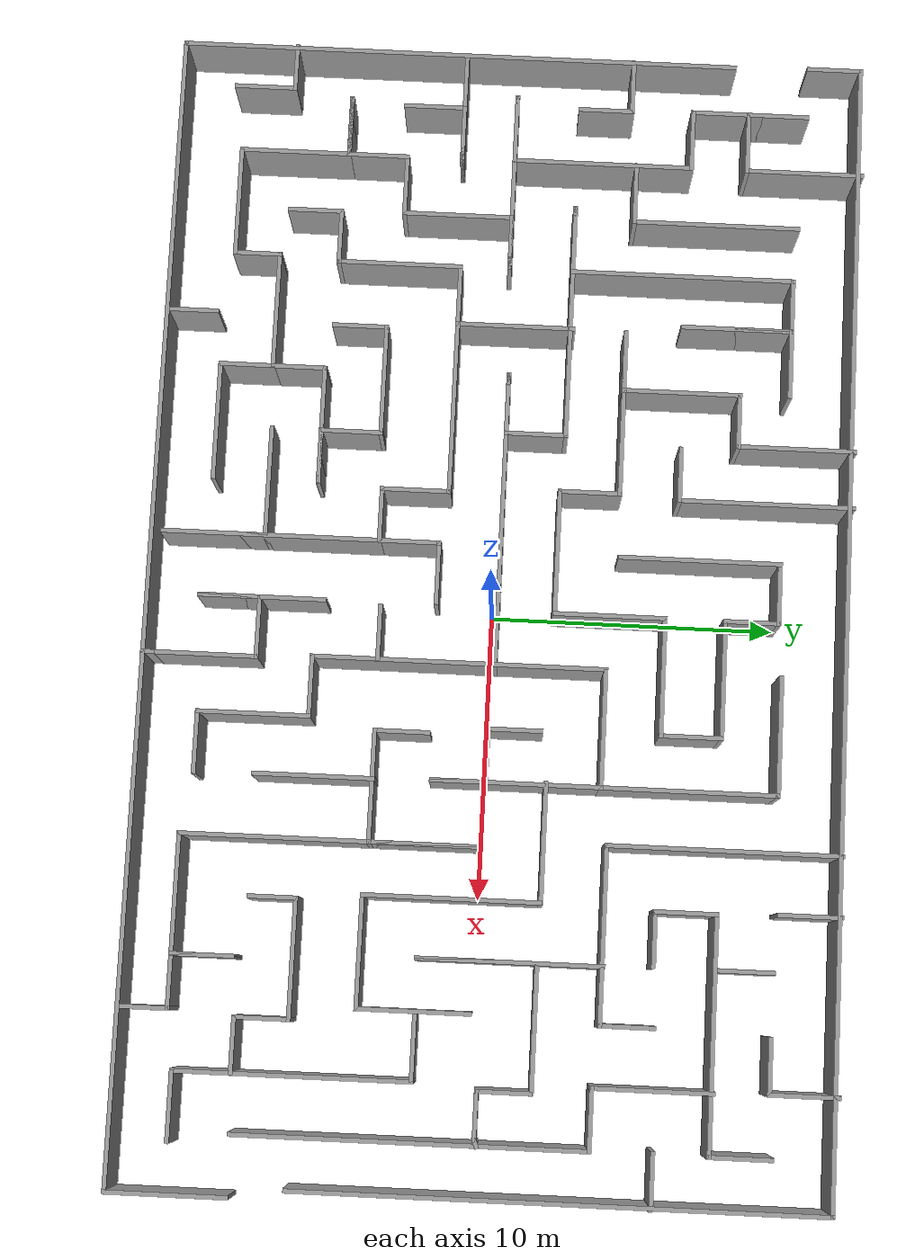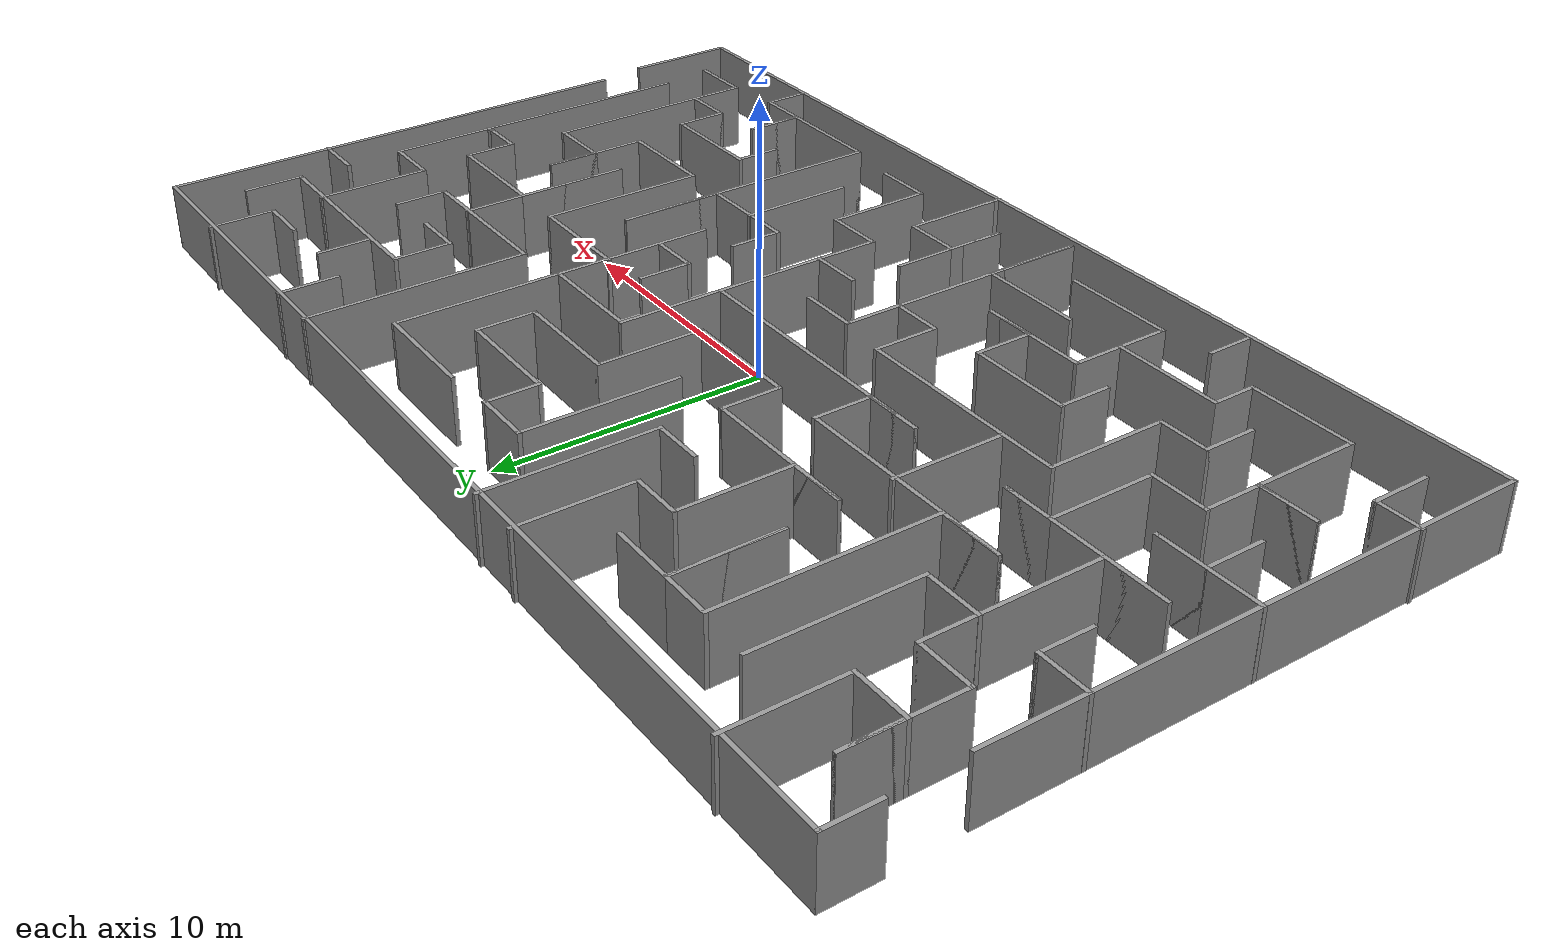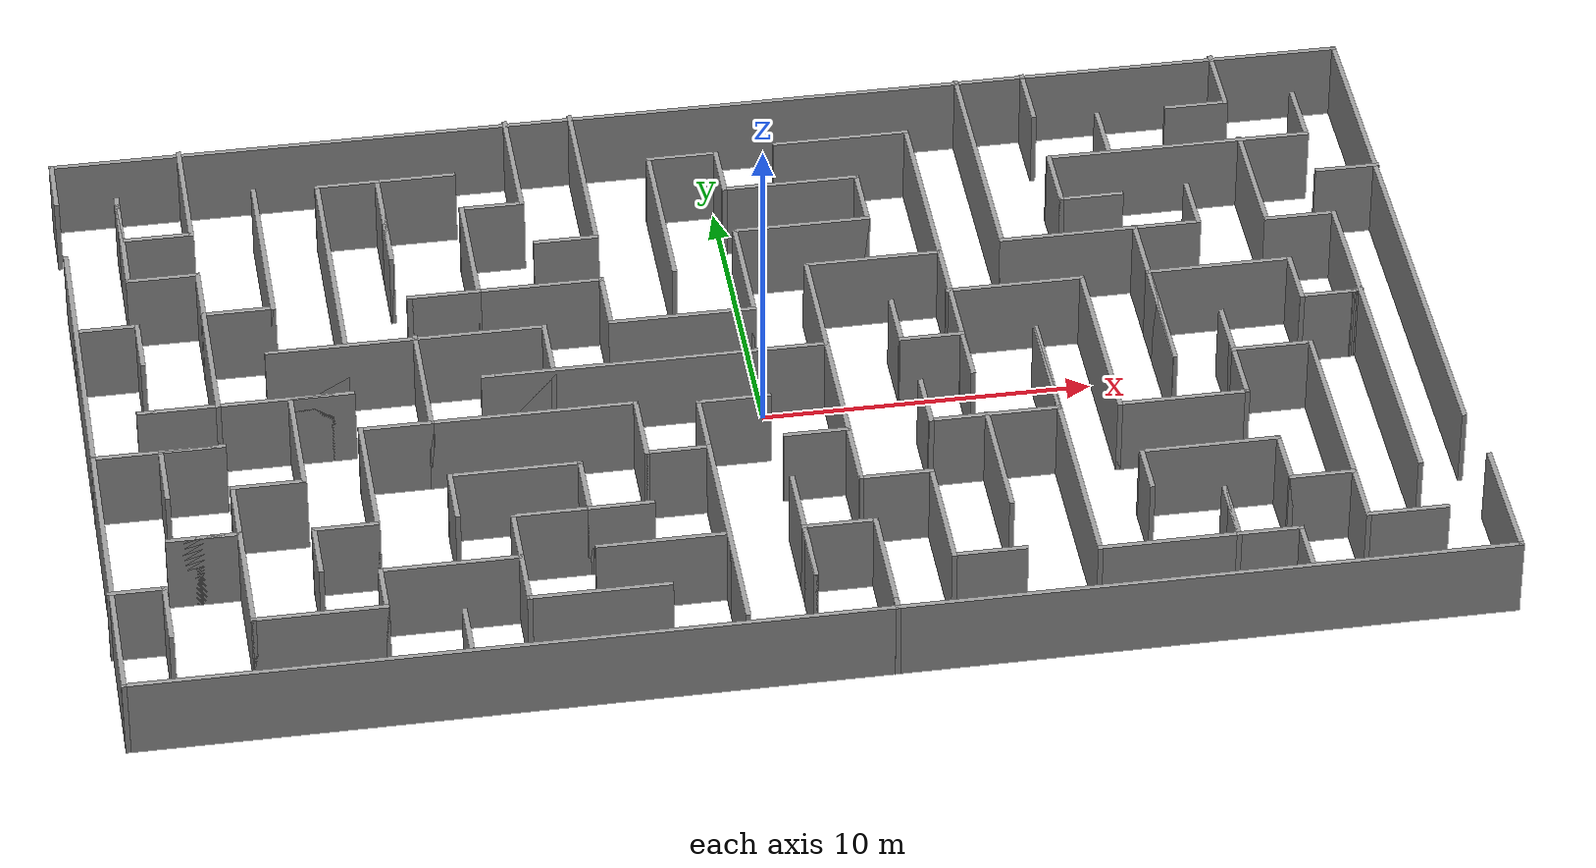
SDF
<?xml version='1.0'?>
<sdf version='1.7'>
  <model name='maze_model'>
    <pose>0.068092 0.23364 0 0 -0 0</pose>
    <link name='Wall_100'>
      <collision name='Wall_100_Collision'>
        <geometry>
          <box>
            <size>2.25 0.15 2.5</size>
          </box>
        </geometry>
        <pose>0 0 1.25 0 -0 0</pose>
      </collision>
      <visual name='Wall_100_Visual'>
        <pose>0 0 1.25 0 -0 0</pose>
        <geometry>
          <box>
            <size>2.25 0.15 2.5</size>
          </box>
        </geometry>
        <material>
          <script>
            <uri>file://media/materials/scripts/gazebo.material</uri>
            <name>Gazebo/Grey</name>
          </script>
          <ambient>1 1 1 1</ambient>
        </material>
        <meta>
          <layer>0</layer>
        </meta>
      </visual>
      <pose>-9.14508 4.06765 0 0 -0 3.14159</pose>
    </link>
    <link name='Wall_101'>
      <collision name='Wall_101_Collision'>
        <geometry>
          <box>
            <size>6 0.15 2.5</size>
          </box>
        </geometry>
        <pose>0 0 1.25 0 -0 0</pose>
      </collision>
      <visual name='Wall_101_Visual'>
        <pose>0 0 1.25 0 -0 0</pose>
        <geometry>
          <box>
            <size>6 0.15 2.5</size>
          </box>
        </geometry>
        <material>
          <script>
            <uri>file://media/materials/scripts/gazebo.material</uri>
            <name>Gazebo/Grey</name>
          </script>
          <ambient>1 1 1 1</ambient>
        </material>
        <meta>
          <layer>0</layer>
        </meta>
      </visual>
      <pose>-7.27008 4.06765 0 0 -0 0</pose>
    </link>
    <link name='Wall_102'>
      <collision name='Wall_102_Collision'>
        <geometry>
          <box>
            <size>2.25 0.15 2.5</size>
          </box>
        </geometry>
        <pose>0 0 1.25 0 -0 0</pose>
      </collision>
      <visual name='Wall_102_Visual'>
        <pose>0 0 1.25 0 -0 0</pose>
        <geometry>
          <box>
            <size>2.25 0.15 2.5</size>
          </box>
        </geometry>
        <material>
          <script>
            <uri>file://media/materials/scripts/gazebo.material</uri>
            <name>Gazebo/Grey</name>
          </script>
          <ambient>1 1 1 1</ambient>
        </material>
        <meta>
          <layer>0</layer>
        </meta>
      </visual>
      <pose>-4.34508 3.01765 0 0 -0 -1.5708</pose>
    </link>
    <link name='Wall_103'>
      <collision name='Wall_103_Collision'>
        <geometry>
          <box>
            <size>4.5 0.15 2.5</size>
          </box>
        </geometry>
        <pose>0 0 1.25 0 -0 0</pose>
      </collision>
      <visual name='Wall_103_Visual'>
        <pose>0 0 1.25 0 -0 0</pose>
        <geometry>
          <box>
            <size>4.5 0.15 2.5</size>
          </box>
        </geometry>
        <material>
          <script>
            <uri>file://media/materials/scripts/gazebo.material</uri>
            <name>Gazebo/Grey</name>
          </script>
          <ambient>1 1 1 1</ambient>
        </material>
        <meta>
          <layer>0</layer>
        </meta>
      </visual>
      <pose>-2.17008 1.96765 0 0 -0 0</pose>
    </link>
    <link name='Wall_104'>
      <collision name='Wall_104_Collision'>
        <geometry>
          <box>
            <size>4 0.15 2.5</size>
          </box>
        </geometry>
        <pose>0 0 1.25 0 -0 0</pose>
      </collision>
      <visual name='Wall_104_Visual'>
        <pose>0 0 1.25 0 -0 0</pose>
        <geometry>
          <box>
            <size>4 0.15 2.5</size>
          </box>
        </geometry>
        <material>
          <script>
            <uri>file://media/materials/scripts/gazebo.material</uri>
            <name>Gazebo/Grey</name>
          </script>
          <ambient>1 1 1 1</ambient>
        </material>
        <meta>
          <layer>0</layer>
        </meta>
      </visual>
      <pose>0.004921 3.89265 0 0 -0 1.5708</pose>
    </link>
    <link name='Wall_105'>
      <collision name='Wall_105_Collision'>
        <geometry>
          <box>
            <size>4.25 0.15 2.5</size>
          </box>
        </geometry>
        <pose>0 0 1.25 0 -0 0</pose>
      </collision>
      <visual name='Wall_105_Visual'>
        <pose>0 0 1.25 0 -0 0</pose>
        <geometry>
          <box>
            <size>4.25 0.15 2.5</size>
          </box>
        </geometry>
        <material>
          <script>
            <uri>file://media/materials/scripts/gazebo.material</uri>
            <name>Gazebo/Grey</name>
          </script>
          <ambient>1 1 1 1</ambient>
        </material>
        <meta>
          <layer>0</layer>
        </meta>
      </visual>
      <pose>2.05492 5.81765 0 0 -0 0</pose>
    </link>
    <link name='Wall_106'>
      <collision name='Wall_106_Collision'>
        <geometry>
          <box>
            <size>2.25 0.15 2.5</size>
          </box>
        </geometry>
        <pose>0 0 1.25 0 -0 0</pose>
      </collision>
      <visual name='Wall_106_Visual'>
        <pose>0 0 1.25 0 -0 0</pose>
        <geometry>
          <box>
            <size>2.25 0.15 2.5</size>
          </box>
        </geometry>
        <material>
          <script>
            <uri>file://media/materials/scripts/gazebo.material</uri>
            <name>Gazebo/Grey</name>
          </script>
          <ambient>1 1 1 1</ambient>
        </material>
        <meta>
          <layer>0</layer>
        </meta>
      </visual>
      <pose>4.10492 6.86765 0 0 -0 1.5708</pose>
    </link>
    <link name='Wall_107'>
      <collision name='Wall_107_Collision'>
        <geometry>
          <box>
            <size>4.25 0.15 2.5</size>
          </box>
        </geometry>
        <pose>0 0 1.25 0 -0 0</pose>
      </collision>
      <visual name='Wall_107_Visual'>
        <pose>0 0 1.25 0 -0 0</pose>
        <geometry>
          <box>
            <size>4.25 0.15 2.5</size>
          </box>
        </geometry>
        <material>
          <script>
            <uri>file://media/materials/scripts/gazebo.material</uri>
            <name>Gazebo/Grey</name>
          </script>
          <ambient>1 1 1 1</ambient>
        </material>
        <meta>
          <layer>0</layer>
        </meta>
      </visual>
      <pose>2.05492 7.91765 0 0 -0 3.14159</pose>
    </link>
    <link name='Wall_108'>
      <collision name='Wall_108_Collision'>
        <geometry>
          <box>
            <size>2 0.15 2.5</size>
          </box>
        </geometry>
        <pose>0 0 1.25 0 -0 0</pose>
      </collision>
      <visual name='Wall_108_Visual'>
        <pose>0 0 1.25 0 -0 0</pose>
        <geometry>
          <box>
            <size>2 0.15 2.5</size>
          </box>
        </geometry>
        <material>
          <script>
            <uri>file://media/materials/scripts/gazebo.material</uri>
            <name>Gazebo/Grey</name>
          </script>
          <ambient>1 1 1 1</ambient>
        </material>
        <meta>
          <layer>0</layer>
        </meta>
      </visual>
      <pose>0.004921 8.84265 0 0 -0 1.5708</pose>
    </link>
    <link name='Wall_109'>
      <collision name='Wall_109_Collision'>
        <geometry>
          <box>
            <size>2.25 0.15 2.5</size>
          </box>
        </geometry>
        <pose>0 0 1.25 0 -0 0</pose>
      </collision>
      <visual name='Wall_109_Visual'>
        <pose>0 0 1.25 0 -0 0</pose>
        <geometry>
          <box>
            <size>2.25 0.15 2.5</size>
          </box>
        </geometry>
        <material>
          <script>
            <uri>file://media/materials/scripts/gazebo.material</uri>
            <name>Gazebo/Grey</name>
          </script>
          <ambient>1 1 1 1</ambient>
        </material>
        <meta>
          <layer>0</layer>
        </meta>
      </visual>
      <pose>-1.04508 9.76765 0 0 -0 3.14159</pose>
    </link>
    <link name='Wall_110'>
      <collision name='Wall_110_Collision'>
        <geometry>
          <box>
            <size>5.75 0.15 2.5</size>
          </box>
        </geometry>
        <pose>0 0 1.25 0 -0 0</pose>
      </collision>
      <visual name='Wall_110_Visual'>
        <pose>0 0 1.25 0 -0 0</pose>
        <geometry>
          <box>
            <size>5.75 0.15 2.5</size>
          </box>
        </geometry>
        <material>
          <script>
            <uri>file://media/materials/scripts/gazebo.material</uri>
            <name>Gazebo/Grey</name>
          </script>
          <ambient>1 1 1 1</ambient>
        </material>
        <meta>
          <layer>0</layer>
        </meta>
      </visual>
      <pose>-2.09508 6.96765 0 0 -0 -1.5708</pose>
    </link>
    <link name='Wall_112'>
      <collision name='Wall_112_Collision'>
        <geometry>
          <box>
            <size>6.25 0.15 2.5</size>
          </box>
        </geometry>
        <pose>0 0 1.25 0 -0 0</pose>
      </collision>
      <visual name='Wall_112_Visual'>
        <pose>0 0 1.25 0 -0 0</pose>
        <geometry>
          <box>
            <size>6.25 0.15 2.5</size>
          </box>
        </geometry>
        <material>
          <script>
            <uri>file://media/materials/scripts/gazebo.material</uri>
            <name>Gazebo/Grey</name>
          </script>
          <ambient>1 1 1 1</ambient>
        </material>
        <meta>
          <layer>0</layer>
        </meta>
      </visual>
      <pose>-4.21466 9.21765 0 0 -0 -1.5708</pose>
    </link>
    <link name='Wall_113'>
      <collision name='Wall_113_Collision'>
        <geometry>
          <box>
            <size>2 0.15 2.5</size>
          </box>
        </geometry>
        <pose>0 0 1.25 0 -0 0</pose>
      </collision>
      <visual name='Wall_113_Visual'>
        <pose>0 0 1.25 0 -0 0</pose>
        <geometry>
          <box>
            <size>2 0.15 2.5</size>
          </box>
        </geometry>
        <material>
          <script>
            <uri>file://media/materials/scripts/gazebo.material</uri>
            <name>Gazebo/Grey</name>
          </script>
          <ambient>1 1 1 1</ambient>
        </material>
        <meta>
          <layer>0</layer>
        </meta>
      </visual>
      <pose>-5.13966 6.16765 0 0 -0 3.14159</pose>
    </link>
    <link name='Wall_115'>
      <collision name='Wall_115_Collision'>
        <geometry>
          <box>
            <size>4.5 0.15 2.5</size>
          </box>
        </geometry>
        <pose>0 0 1.25 0 -0 0</pose>
      </collision>
      <visual name='Wall_115_Visual'>
        <pose>0 0 1.25 0 -0 0</pose>
        <geometry>
          <box>
            <size>4.5 0.15 2.5</size>
          </box>
        </geometry>
        <material>
          <script>
            <uri>file://media/materials/scripts/gazebo.material</uri>
            <name>Gazebo/Grey</name>
          </script>
          <ambient>1 1 1 1</ambient>
        </material>
        <meta>
          <layer>0</layer>
        </meta>
      </visual>
      <pose>-0.092291 -8.24265 0 0 -0 -1.5708</pose>
    </link>
    <link name='Wall_116'>
      <collision name='Wall_116_Collision'>
        <geometry>
          <box>
            <size>2.25 0.15 2.5</size>
          </box>
        </geometry>
        <pose>0 0 1.25 0 -0 0</pose>
      </collision>
      <visual name='Wall_116_Visual'>
        <pose>0 0 1.25 0 -0 0</pose>
        <geometry>
          <box>
            <size>2.25 0.15 2.5</size>
          </box>
        </geometry>
        <material>
          <script>
            <uri>file://media/materials/scripts/gazebo.material</uri>
            <name>Gazebo/Grey</name>
          </script>
          <ambient>1 1 1 1</ambient>
        </material>
        <meta>
          <layer>0</layer>
        </meta>
      </visual>
      <pose>-0.092291 -9.36765 0 0 -0 1.5708</pose>
    </link>
    <link name='Wall_117'>
      <collision name='Wall_117_Collision'>
        <geometry>
          <box>
            <size>2.25 0.15 2.5</size>
          </box>
        </geometry>
        <pose>0 0 1.25 0 -0 0</pose>
      </collision>
      <visual name='Wall_117_Visual'>
        <pose>0 0 1.25 0 -0 0</pose>
        <geometry>
          <box>
            <size>2.25 0.15 2.5</size>
          </box>
        </geometry>
        <material>
          <script>
            <uri>file://media/materials/scripts/gazebo.material</uri>
            <name>Gazebo/Grey</name>
          </script>
          <ambient>1 1 1 1</ambient>
        </material>
        <meta>
          <layer>0</layer>
        </meta>
      </visual>
      <pose>0.957709 -8.31766 0 0 -0 0</pose>
    </link>
    <link name='Wall_118'>
      <collision name='Wall_118_Collision'>
        <geometry>
          <box>
            <size>3.75 0.15 2.5</size>
          </box>
        </geometry>
        <pose>0 0 1.25 0 -0 0</pose>
      </collision>
      <visual name='Wall_118_Visual'>
        <pose>0 0 1.25 0 -0 0</pose>
        <geometry>
          <box>
            <size>3.75 0.15 2.5</size>
          </box>
        </geometry>
        <material>
          <script>
            <uri>file://media/materials/scripts/gazebo.material</uri>
            <name>Gazebo/Grey</name>
          </script>
          <ambient>1 1 1 1</ambient>
        </material>
        <meta>
          <layer>0</layer>
        </meta>
      </visual>
      <pose>2.00771 -10.1177 0 0 -0 -1.5708</pose>
    </link>
    <link name='Wall_119'>
      <collision name='Wall_119_Collision'>
        <geometry>
          <box>
            <size>0.5 0.15 2.5</size>
          </box>
        </geometry>
        <pose>0 0 1.25 0 -0 0</pose>
      </collision>
      <visual name='Wall_119_Visual'>
        <pose>0 0 1.25 0 -0 0</pose>
        <geometry>
          <box>
            <size>0.5 0.15 2.5</size>
          </box>
        </geometry>
        <material>
          <script>
            <uri>file://media/materials/scripts/gazebo.material</uri>
            <name>Gazebo/Grey</name>
          </script>
          <ambient>1 1 1 1</ambient>
        </material>
        <meta>
          <layer>0</layer>
        </meta>
      </visual>
      <pose>2.00771 -12.0927 0 0 -0 -1.5708</pose>
    </link>
    <link name='Wall_121'>
      <collision name='Wall_121_Collision'>
        <geometry>
          <box>
            <size>4 0.15 2.5</size>
          </box>
        </geometry>
        <pose>0 0 1.25 0 -0 0</pose>
      </collision>
      <visual name='Wall_121_Visual'>
        <pose>0 0 1.25 0 -0 0</pose>
        <geometry>
          <box>
            <size>4 0.15 2.5</size>
          </box>
        </geometry>
        <material>
          <script>
            <uri>file://media/materials/scripts/gazebo.material</uri>
            <name>Gazebo/Grey</name>
          </script>
          <ambient>1 1 1 1</ambient>
        </material>
        <meta>
          <layer>0</layer>
        </meta>
      </visual>
      <pose>1.89756 1.90459 0 0 -0 1.5708</pose>
    </link>
    <link name='Wall_122'>
      <collision name='Wall_122_Collision'>
        <geometry>
          <box>
            <size>4.25 0.15 2.5</size>
          </box>
        </geometry>
        <pose>0 0 1.25 0 -0 0</pose>
      </collision>
      <visual name='Wall_122_Visual'>
        <pose>0 0 1.25 0 -0 0</pose>
        <geometry>
          <box>
            <size>4.25 0.15 2.5</size>
          </box>
        </geometry>
        <material>
          <script>
            <uri>file://media/materials/scripts/gazebo.material</uri>
            <name>Gazebo/Grey</name>
          </script>
          <ambient>1 1 1 1</ambient>
        </material>
        <meta>
          <layer>0</layer>
        </meta>
      </visual>
      <pose>3.94756 3.82959 0 0 -0 0</pose>
    </link>
    <link name='Wall_123'>
      <collision name='Wall_123_Collision'>
        <geometry>
          <box>
            <size>6.25 0.15 2.5</size>
          </box>
        </geometry>
        <pose>0 0 1.25 0 -0 0</pose>
      </collision>
      <visual name='Wall_123_Visual'>
        <pose>0 0 1.25 0 -0 0</pose>
        <geometry>
          <box>
            <size>6.25 0.15 2.5</size>
          </box>
        </geometry>
        <material>
          <script>
            <uri>file://media/materials/scripts/gazebo.material</uri>
            <name>Gazebo/Grey</name>
          </script>
          <ambient>1 1 1 1</ambient>
        </material>
        <meta>
          <layer>0</layer>
        </meta>
      </visual>
      <pose>5.99756 6.87959 0 0 -0 1.5708</pose>
    </link>
    <link name='Wall_124'>
      <collision name='Wall_124_Collision'>
        <geometry>
          <box>
            <size>4.25 0.15 2.5</size>
          </box>
        </geometry>
        <pose>0 0 1.25 0 -0 0</pose>
      </collision>
      <visual name='Wall_124_Visual'>
        <pose>0 0 1.25 0 -0 0</pose>
        <geometry>
          <box>
            <size>4.25 0.15 2.5</size>
          </box>
        </geometry>
        <material>
          <script>
            <uri>file://media/materials/scripts/gazebo.material</uri>
            <name>Gazebo/Grey</name>
          </script>
          <ambient>1 1 1 1</ambient>
        </material>
        <meta>
          <layer>0</layer>
        </meta>
      </visual>
      <pose>3.94756 9.92959 0 0 -0 3.14159</pose>
    </link>
    <link name='Wall_126'>
      <collision name='Wall_126_Collision'>
        <geometry>
          <box>
            <size>6 0.15 2.5</size>
          </box>
        </geometry>
        <pose>0 0 1.25 0 -0 0</pose>
      </collision>
      <visual name='Wall_126_Visual'>
        <pose>0 0 1.25 0 -0 0</pose>
        <geometry>
          <box>
            <size>6 0.15 2.5</size>
          </box>
        </geometry>
        <material>
          <script>
            <uri>file://media/materials/scripts/gazebo.material</uri>
            <name>Gazebo/Grey</name>
          </script>
          <ambient>1 1 1 1</ambient>
        </material>
        <meta>
          <layer>0</layer>
        </meta>
      </visual>
      <pose>5.99756 0.904594 0 0 -0 -1.5708</pose>
    </link>
    <link name='Wall_127'>
      <collision name='Wall_127_Collision'>
        <geometry>
          <box>
            <size>2 0.15 2.5</size>
          </box>
        </geometry>
        <pose>0 0 1.25 0 -0 0</pose>
      </collision>
      <visual name='Wall_127_Visual'>
        <pose>0 0 1.25 0 -0 0</pose>
        <geometry>
          <box>
            <size>2 0.15 2.5</size>
          </box>
        </geometry>
        <material>
          <script>
            <uri>file://media/materials/scripts/gazebo.material</uri>
            <name>Gazebo/Grey</name>
          </script>
          <ambient>1 1 1 1</ambient>
        </material>
        <meta>
          <layer>0</layer>
        </meta>
      </visual>
      <pose>5.99756 -1.09541 0 0 -0 1.5708</pose>
    </link>
    <link name='Wall_128'>
      <collision name='Wall_128_Collision'>
        <geometry>
          <box>
            <size>2 0.15 2.5</size>
          </box>
        </geometry>
        <pose>0 0 1.25 0 -0 0</pose>
      </collision>
      <visual name='Wall_128_Visual'>
        <pose>0 0 1.25 0 -0 0</pose>
        <geometry>
          <box>
            <size>2 0.15 2.5</size>
          </box>
        </geometry>
        <material>
          <script>
            <uri>file://media/materials/scripts/gazebo.material</uri>
            <name>Gazebo/Grey</name>
          </script>
          <ambient>1 1 1 1</ambient>
        </material>
        <meta>
          <layer>0</layer>
        </meta>
      </visual>
      <pose>5.07256 -0.170406 0 0 -0 3.14159</pose>
    </link>
    <link name='Wall_129'>
      <collision name='Wall_129_Collision'>
        <geometry>
          <box>
            <size>2 0.15 2.5</size>
          </box>
        </geometry>
        <pose>0 0 1.25 0 -0 0</pose>
      </collision>
      <visual name='Wall_129_Visual'>
        <pose>0 0 1.25 0 -0 0</pose>
        <geometry>
          <box>
            <size>2 0.15 2.5</size>
          </box>
        </geometry>
        <material>
          <script>
            <uri>file://media/materials/scripts/gazebo.material</uri>
            <name>Gazebo/Grey</name>
          </script>
          <ambient>1 1 1 1</ambient>
        </material>
        <meta>
          <layer>0</layer>
        </meta>
      </visual>
      <pose>4.14756 0.754594 0 0 -0 1.5708</pose>
    </link>
    <link name='Wall_131'>
      <collision name='Wall_131_Collision'>
        <geometry>
          <box>
            <size>4.25 0.15 2.5</size>
          </box>
        </geometry>
        <pose>0 0 1.25 0 -0 0</pose>
      </collision>
      <visual name='Wall_131_Visual'>
        <pose>0 0 1.25 0 -0 0</pose>
        <geometry>
          <box>
            <size>4.25 0.15 2.5</size>
          </box>
        </geometry>
        <material>
          <script>
            <uri>file://media/materials/scripts/gazebo.material</uri>
            <name>Gazebo/Grey</name>
          </script>
          <ambient>1 1 1 1</ambient>
        </material>
        <meta>
          <layer>0</layer>
        </meta>
      </visual>
      <pose>7.98744 1.93097 0 0 -0 0</pose>
    </link>
    <link name='Wall_132'>
      <collision name='Wall_132_Collision'>
        <geometry>
          <box>
            <size>6.25 0.15 2.5</size>
          </box>
        </geometry>
        <pose>0 0 1.25 0 -0 0</pose>
      </collision>
      <visual name='Wall_132_Visual'>
        <pose>0 0 1.25 0 -0 0</pose>
        <geometry>
          <box>
            <size>6.25 0.15 2.5</size>
          </box>
        </geometry>
        <material>
          <script>
            <uri>file://media/materials/scripts/gazebo.material</uri>
            <name>Gazebo/Grey</name>
          </script>
          <ambient>1 1 1 1</ambient>
        </material>
        <meta>
          <layer>0</layer>
        </meta>
      </visual>
      <pose>10.0374 -1.11903 0 0 -0 -1.5708</pose>
    </link>
    <link name='Wall_133'>
      <collision name='Wall_133_Collision'>
        <geometry>
          <box>
            <size>4 0.15 2.5</size>
          </box>
        </geometry>
        <pose>0 0 1.25 0 -0 0</pose>
      </collision>
      <visual name='Wall_133_Visual'>
        <pose>0 0 1.25 0 -0 0</pose>
        <geometry>
          <box>
            <size>4 0.15 2.5</size>
          </box>
        </geometry>
        <material>
          <script>
            <uri>file://media/materials/scripts/gazebo.material</uri>
            <name>Gazebo/Grey</name>
          </script>
          <ambient>1 1 1 1</ambient>
        </material>
        <meta>
          <layer>0</layer>
        </meta>
      </visual>
      <pose>11.9624 -4.16903 0 0 -0 0</pose>
    </link>
    <link name='Wall_134'>
      <collision name='Wall_134_Collision'>
        <geometry>
          <box>
            <size>4 0.15 2.5</size>
          </box>
        </geometry>
        <pose>0 0 1.25 0 -0 0</pose>
      </collision>
      <visual name='Wall_134_Visual'>
        <pose>0 0 1.25 0 -0 0</pose>
        <geometry>
          <box>
            <size>4 0.15 2.5</size>
          </box>
        </geometry>
        <material>
          <script>
            <uri>file://media/materials/scripts/gazebo.material</uri>
            <name>Gazebo/Grey</name>
          </script>
          <ambient>1 1 1 1</ambient>
        </material>
        <meta>
          <layer>0</layer>
        </meta>
      </visual>
      <pose>13.8874 -2.24403 0 0 -0 1.5708</pose>
    </link>
    <link name='Wall_135'>
      <collision name='Wall_135_Collision'>
        <geometry>
          <box>
            <size>2 0.15 2.5</size>
          </box>
        </geometry>
        <pose>0 0 1.25 0 -0 0</pose>
      </collision>
      <visual name='Wall_135_Visual'>
        <pose>0 0 1.25 0 -0 0</pose>
        <geometry>
          <box>
            <size>2 0.15 2.5</size>
          </box>
        </geometry>
        <material>
          <script>
            <uri>file://media/materials/scripts/gazebo.material</uri>
            <name>Gazebo/Grey</name>
          </script>
          <ambient>1 1 1 1</ambient>
        </material>
        <meta>
          <layer>0</layer>
        </meta>
      </visual>
      <pose>13.8874 -1.24403 0 0 -0 -1.5708</pose>
    </link>
    <link name='Wall_136'>
      <collision name='Wall_136_Collision'>
        <geometry>
          <box>
            <size>2.5 0.15 2.5</size>
          </box>
        </geometry>
        <pose>0 0 1.25 0 -0 0</pose>
      </collision>
      <visual name='Wall_136_Visual'>
        <pose>0 0 1.25 0 -0 0</pose>
        <geometry>
          <box>
            <size>2.5 0.15 2.5</size>
          </box>
        </geometry>
        <material>
          <script>
            <uri>file://media/materials/scripts/gazebo.material</uri>
            <name>Gazebo/Grey</name>
          </script>
          <ambient>1 1 1 1</ambient>
        </material>
        <meta>
          <layer>0</layer>
        </meta>
      </visual>
      <pose>15.0624 -2.16903 0 0 -0 0</pose>
    </link>
    <link name='Wall_137'>
      <collision name='Wall_137_Collision'>
        <geometry>
          <box>
            <size>8.25 0.15 2.5</size>
          </box>
        </geometry>
        <pose>0 0 1.25 0 -0 0</pose>
      </collision>
      <visual name='Wall_137_Visual'>
        <pose>0 0 1.25 0 -0 0</pose>
        <geometry>
          <box>
            <size>8.25 0.15 2.5</size>
          </box>
        </geometry>
        <material>
          <script>
            <uri>file://media/materials/scripts/gazebo.material</uri>
            <name>Gazebo/Grey</name>
          </script>
          <ambient>1 1 1 1</ambient>
        </material>
        <meta>
          <layer>0</layer>
        </meta>
      </visual>
      <pose>16.2374 -6.21903 0 0 -0 -1.5708</pose>
    </link>
    <link name='Wall_138'>
      <collision name='Wall_138_Collision'>
        <geometry>
          <box>
            <size>2.5 0.15 2.5</size>
          </box>
        </geometry>
        <pose>0 0 1.25 0 -0 0</pose>
      </collision>
      <visual name='Wall_138_Visual'>
        <pose>0 0 1.25 0 -0 0</pose>
        <geometry>
          <box>
            <size>2.5 0.15 2.5</size>
          </box>
        </geometry>
        <material>
          <script>
            <uri>file://media/materials/scripts/gazebo.material</uri>
            <name>Gazebo/Grey</name>
          </script>
          <ambient>1 1 1 1</ambient>
        </material>
        <meta>
          <layer>0</layer>
        </meta>
      </visual>
      <pose>17.4124 -10.269 0 0 -0 0</pose>
    </link>
    <link name='Wall_14'>
      <collision name='Wall_14_Collision'>
        <geometry>
          <box>
            <size>40.5 0.15 2.5</size>
          </box>
        </geometry>
        <pose>0 0 1.25 0 -0 0</pose>
      </collision>
      <visual name='Wall_14_Visual'>
        <pose>0 0 1.25 0 -0 0</pose>
        <geometry>
          <box>
            <size>40.5 0.15 2.5</size>
          </box>
        </geometry>
        <material>
          <script>
            <uri>file://media/materials/scripts/gazebo.material</uri>
            <name>Gazebo/Grey</name>
          </script>
          <ambient>1 1 1 1</ambient>
        </material>
        <meta>
          <layer>0</layer>
        </meta>
      </visual>
      <pose>-0.159962 12.1446 0 0 -0 0</pose>
    </link>
    <link name='Wall_140'>
      <collision name='Wall_140_Collision'>
        <geometry>
          <box>
            <size>2 0.15 2.5</size>
          </box>
        </geometry>
        <pose>0 0 1.25 0 -0 0</pose>
      </collision>
      <visual name='Wall_140_Visual'>
        <pose>0 0 1.25 0 -0 0</pose>
        <geometry>
          <box>
            <size>2 0.15 2.5</size>
          </box>
        </geometry>
        <material>
          <script>
            <uri>file://media/materials/scripts/gazebo.material</uri>
            <name>Gazebo/Grey</name>
          </script>
          <ambient>1 1 1 1</ambient>
        </material>
        <meta>
          <layer>0</layer>
        </meta>
      </visual>
      <pose>15.2876 -8.28266 0 0 -0 3.14159</pose>
    </link>
    <link name='Wall_141'>
      <collision name='Wall_141_Collision'>
        <geometry>
          <box>
            <size>2 0.15 2.5</size>
          </box>
        </geometry>
        <pose>0 0 1.25 0 -0 0</pose>
      </collision>
      <visual name='Wall_141_Visual'>
        <pose>0 0 1.25 0 -0 0</pose>
        <geometry>
          <box>
            <size>2 0.15 2.5</size>
          </box>
        </geometry>
        <material>
          <script>
            <uri>file://media/materials/scripts/gazebo.material</uri>
            <name>Gazebo/Grey</name>
          </script>
          <ambient>1 1 1 1</ambient>
        </material>
        <meta>
          <layer>0</layer>
        </meta>
      </visual>
      <pose>14.3626 -7.35766 0 0 -0 1.5708</pose>
    </link>
    <link name='Wall_142'>
      <collision name='Wall_142_Collision'>
        <geometry>
          <box>
            <size>4.25 0.15 2.5</size>
          </box>
        </geometry>
        <pose>0 0 1.25 0 -0 0</pose>
      </collision>
      <visual name='Wall_142_Visual'>
        <pose>0 0 1.25 0 -0 0</pose>
        <geometry>
          <box>
            <size>4.25 0.15 2.5</size>
          </box>
        </geometry>
        <material>
          <script>
            <uri>file://media/materials/scripts/gazebo.material</uri>
            <name>Gazebo/Grey</name>
          </script>
          <ambient>1 1 1 1</ambient>
        </material>
        <meta>
          <layer>0</layer>
        </meta>
      </visual>
      <pose>12.3126 -6.43266 0 0 -0 3.14159</pose>
    </link>
    <link name='Wall_145'>
      <collision name='Wall_145_Collision'>
        <geometry>
          <box>
            <size>1.75 0.15 2.5</size>
          </box>
        </geometry>
        <pose>0 0 1.25 0 -0 0</pose>
      </collision>
      <visual name='Wall_145_Visual'>
        <pose>0 0 1.25 0 -0 0</pose>
        <geometry>
          <box>
            <size>1.75 0.15 2.5</size>
          </box>
        </geometry>
        <material>
          <script>
            <uri>file://media/materials/scripts/gazebo.material</uri>
            <name>Gazebo/Grey</name>
          </script>
          <ambient>1 1 1 1</ambient>
        </material>
        <meta>
          <layer>0</layer>
        </meta>
      </visual>
      <pose>10.2626 -7.23266 0 0 -0 -1.5708</pose>
    </link>
    <link name='Wall_147'>
      <collision name='Wall_147_Collision'>
        <geometry>
          <box>
            <size>1.75 0.15 2.5</size>
          </box>
        </geometry>
        <pose>0 0 1.25 0 -0 0</pose>
      </collision>
      <visual name='Wall_147_Visual'>
        <pose>0 0 1.25 0 -0 0</pose>
        <geometry>
          <box>
            <size>1.75 0.15 2.5</size>
          </box>
        </geometry>
        <material>
          <script>
            <uri>file://media/materials/scripts/gazebo.material</uri>
            <name>Gazebo/Grey</name>
          </script>
          <ambient>1 1 1 1</ambient>
        </material>
        <meta>
          <layer>0</layer>
        </meta>
      </visual>
      <pose>14.1822 -11.3589 0 0 -0 1.5708</pose>
    </link>
    <link name='Wall_148'>
      <collision name='Wall_148_Collision'>
        <geometry>
          <box>
            <size>2 0.15 2.5</size>
          </box>
        </geometry>
        <pose>0 0 1.25 0 -0 0</pose>
      </collision>
      <visual name='Wall_148_Visual'>
        <pose>0 0 1.25 0 -0 0</pose>
        <geometry>
          <box>
            <size>2 0.15 2.5</size>
          </box>
        </geometry>
        <material>
          <script>
            <uri>file://media/materials/scripts/gazebo.material</uri>
            <name>Gazebo/Grey</name>
          </script>
          <ambient>1 1 1 1</ambient>
        </material>
        <meta>
          <layer>0</layer>
        </meta>
      </visual>
      <pose>13.2572 -10.5589 0 0 -0 3.14159</pose>
    </link>
    <link name='Wall_149'>
      <collision name='Wall_149_Collision'>
        <geometry>
          <box>
            <size>2.25 0.15 2.5</size>
          </box>
        </geometry>
        <pose>0 0 1.25 0 -0 0</pose>
      </collision>
      <visual name='Wall_149_Visual'>
        <pose>0 0 1.25 0 -0 0</pose>
        <geometry>
          <box>
            <size>2.25 0.15 2.5</size>
          </box>
        </geometry>
        <material>
          <script>
            <uri>file://media/materials/scripts/gazebo.material</uri>
            <name>Gazebo/Grey</name>
          </script>
          <ambient>1 1 1 1</ambient>
        </material>
        <meta>
          <layer>0</layer>
        </meta>
      </visual>
      <pose>12.3322 -9.50891 0 0 -0 1.5708</pose>
    </link>
    <link name='Wall_15'>
      <collision name='Wall_15_Collision'>
        <geometry>
          <box>
            <size>18.5 0.15 2.5</size>
          </box>
        </geometry>
        <pose>0 0 1.25 0 -0 0</pose>
      </collision>
      <visual name='Wall_15_Visual'>
        <pose>0 0 1.25 0 -0 0</pose>
        <geometry>
          <box>
            <size>18.5 0.15 2.5</size>
          </box>
        </geometry>
        <material>
          <script>
            <uri>file://media/materials/scripts/gazebo.material</uri>
            <name>Gazebo/Grey</name>
          </script>
          <ambient>1 1 1 1</ambient>
        </material>
        <meta>
          <layer>0</layer>
        </meta>
      </visual>
      <pose>20.015 2.9696 0 0 -0 -1.5708</pose>
    </link>
    <link name='Wall_150'>
      <collision name='Wall_150_Collision'>
        <geometry>
          <box>
            <size>2.25 0.15 2.5</size>
          </box>
        </geometry>
        <pose>0 0 1.25 0 -0 0</pose>
      </collision>
      <visual name='Wall_150_Visual'>
        <pose>0 0 1.25 0 -0 0</pose>
        <geometry>
          <box>
            <size>2.25 0.15 2.5</size>
          </box>
        </geometry>
        <material>
          <script>
            <uri>file://media/materials/scripts/gazebo.material</uri>
            <name>Gazebo/Grey</name>
          </script>
          <ambient>1 1 1 1</ambient>
        </material>
        <meta>
          <layer>0</layer>
        </meta>
      </visual>
      <pose>12.3322 -9.50891 0 0 -0 -1.5708</pose>
    </link>
    <link name='Wall_151'>
      <collision name='Wall_151_Collision'>
        <geometry>
          <box>
            <size>4.25 0.15 2.5</size>
          </box>
        </geometry>
        <pose>0 0 1.25 0 -0 0</pose>
      </collision>
      <visual name='Wall_151_Visual'>
        <pose>0 0 1.25 0 -0 0</pose>
        <geometry>
          <box>
            <size>4.25 0.15 2.5</size>
          </box>
        </geometry>
        <material>
          <script>
            <uri>file://media/materials/scripts/gazebo.material</uri>
            <name>Gazebo/Grey</name>
          </script>
          <ambient>1 1 1 1</ambient>
        </material>
        <meta>
          <layer>0</layer>
        </meta>
      </visual>
      <pose>10.2822 -10.5589 0 0 -0 3.14159</pose>
    </link>
    <link name='Wall_152'>
      <collision name='Wall_152_Collision'>
        <geometry>
          <box>
            <size>10.5 0.15 2.5</size>
          </box>
        </geometry>
        <pose>0 0 1.25 0 -0 0</pose>
      </collision>
      <visual name='Wall_152_Visual'>
        <pose>0 0 1.25 0 -0 0</pose>
        <geometry>
          <box>
            <size>10.5 0.15 2.5</size>
          </box>
        </geometry>
        <material>
          <script>
            <uri>file://media/materials/scripts/gazebo.material</uri>
            <name>Gazebo/Grey</name>
          </script>
          <ambient>1 1 1 1</ambient>
        </material>
        <meta>
          <layer>0</layer>
        </meta>
      </visual>
      <pose>8.23218 -5.38391 0 0 -0 1.5708</pose>
    </link>
    <link name='Wall_153'>
      <collision name='Wall_153_Collision'>
        <geometry>
          <box>
            <size>4 0.15 2.5</size>
          </box>
        </geometry>
        <pose>0 0 1.25 0 -0 0</pose>
      </collision>
      <visual name='Wall_153_Visual'>
        <pose>0 0 1.25 0 -0 0</pose>
        <geometry>
          <box>
            <size>4 0.15 2.5</size>
          </box>
        </geometry>
        <material>
          <script>
            <uri>file://media/materials/scripts/gazebo.material</uri>
            <name>Gazebo/Grey</name>
          </script>
          <ambient>1 1 1 1</ambient>
        </material>
        <meta>
          <layer>0</layer>
        </meta>
      </visual>
      <pose>8.23218 -2.13391 0 0 -0 -1.5708</pose>
    </link>
    <link name='Wall_154'>
      <collision name='Wall_154_Collision'>
        <geometry>
          <box>
            <size>4 0.15 2.5</size>
          </box>
        </geometry>
        <pose>0 0 1.25 0 -0 0</pose>
      </collision>
      <visual name='Wall_154_Visual'>
        <pose>0 0 1.25 0 -0 0</pose>
        <geometry>
          <box>
            <size>4 0.15 2.5</size>
          </box>
        </geometry>
        <material>
          <script>
            <uri>file://media/materials/scripts/gazebo.material</uri>
            <name>Gazebo/Grey</name>
          </script>
          <ambient>1 1 1 1</ambient>
        </material>
        <meta>
          <layer>0</layer>
        </meta>
      </visual>
      <pose>6.30718 -4.05891 0 0 -0 3.14159</pose>
    </link>
    <link name='Wall_155'>
      <collision name='Wall_155_Collision'>
        <geometry>
          <box>
            <size>2 0.15 2.5</size>
          </box>
        </geometry>
        <pose>0 0 1.25 0 -0 0</pose>
      </collision>
      <visual name='Wall_155_Visual'>
        <pose>0 0 1.25 0 -0 0</pose>
        <geometry>
          <box>
            <size>2 0.15 2.5</size>
          </box>
        </geometry>
        <material>
          <script>
            <uri>file://media/materials/scripts/gazebo.material</uri>
            <name>Gazebo/Grey</name>
          </script>
          <ambient>1 1 1 1</ambient>
        </material>
        <meta>
          <layer>0</layer>
        </meta>
      </visual>
      <pose>4.38218 -3.13391 0 0 -0 1.5708</pose>
    </link>
    <link name='Wall_157'>
      <collision name='Wall_157_Collision'>
        <geometry>
          <box>
            <size>4.25 0.15 2.5</size>
          </box>
        </geometry>
        <pose>0 0 1.25 0 -0 0</pose>
      </collision>
      <visual name='Wall_157_Visual'>
        <pose>0 0 1.25 0 -0 0</pose>
        <geometry>
          <box>
            <size>4.25 0.15 2.5</size>
          </box>
        </geometry>
        <material>
          <script>
            <uri>file://media/materials/scripts/gazebo.material</uri>
            <name>Gazebo/Grey</name>
          </script>
          <ambient>1 1 1 1</ambient>
        </material>
        <meta>
          <layer>0</layer>
        </meta>
      </visual>
      <pose>6.0605 -6.08723 0 0 -0 -1.5708</pose>
    </link>
    <link name='Wall_159'>
      <collision name='Wall_159_Collision'>
        <geometry>
          <box>
            <size>2 0.15 2.5</size>
          </box>
        </geometry>
        <pose>0 0 1.25 0 -0 0</pose>
      </collision>
      <visual name='Wall_159_Visual'>
        <pose>0 0 1.25 0 -0 0</pose>
        <geometry>
          <box>
            <size>2 0.15 2.5</size>
          </box>
        </geometry>
        <material>
          <script>
            <uri>file://media/materials/scripts/gazebo.material</uri>
            <name>Gazebo/Grey</name>
          </script>
          <ambient>1 1 1 1</ambient>
        </material>
        <meta>
          <layer>0</layer>
        </meta>
      </visual>
      <pose>0.951601 -4.09876 0 0 -0 3.14159</pose>
    </link>
    <link name='Wall_161'>
      <collision name='Wall_161_Collision'>
        <geometry>
          <box>
            <size>8.25 0.15 2.5</size>
          </box>
        </geometry>
        <pose>0 0 1.25 0 -0 0</pose>
      </collision>
      <visual name='Wall_161_Visual'>
        <pose>0 0 1.25 0 -0 0</pose>
        <geometry>
          <box>
            <size>8.25 0.15 2.5</size>
          </box>
        </geometry>
        <material>
          <script>
            <uri>file://media/materials/scripts/gazebo.material</uri>
            <name>Gazebo/Grey</name>
          </script>
          <ambient>1 1 1 1</ambient>
        </material>
        <meta>
          <layer>0</layer>
        </meta>
      </visual>
      <pose>7.96786 8.15612 0 0 -0 -1.5708</pose>
    </link>
    <link name='Wall_162'>
      <collision name='Wall_162_Collision'>
        <geometry>
          <box>
            <size>6.25 0.15 2.5</size>
          </box>
        </geometry>
        <pose>0 0 1.25 0 -0 0</pose>
      </collision>
      <visual name='Wall_162_Visual'>
        <pose>0 0 1.25 0 -0 0</pose>
        <geometry>
          <box>
            <size>6.25 0.15 2.5</size>
          </box>
        </geometry>
        <material>
          <script>
            <uri>file://media/materials/scripts/gazebo.material</uri>
            <name>Gazebo/Grey</name>
          </script>
          <ambient>1 1 1 1</ambient>
        </material>
        <meta>
          <layer>0</layer>
        </meta>
      </visual>
      <pose>11.0179 4.10612 0 0 -0 0</pose>
    </link>
    <link name='Wall_163'>
      <collision name='Wall_163_Collision'>
        <geometry>
          <box>
            <size>2 0.15 2.5</size>
          </box>
        </geometry>
        <pose>0 0 1.25 0 -0 0</pose>
      </collision>
      <visual name='Wall_163_Visual'>
        <pose>0 0 1.25 0 -0 0</pose>
        <geometry>
          <box>
            <size>2 0.15 2.5</size>
          </box>
        </geometry>
        <material>
          <script>
            <uri>file://media/materials/scripts/gazebo.material</uri>
            <name>Gazebo/Grey</name>
          </script>
          <ambient>1 1 1 1</ambient>
        </material>
        <meta>
          <layer>0</layer>
        </meta>
      </visual>
      <pose>14.0679 5.03113 0 0 -0 1.5708</pose>
    </link>
    <link name='Wall_165'>
      <collision name='Wall_165_Collision'>
        <geometry>
          <box>
            <size>2.25 0.15 2.5</size>
          </box>
        </geometry>
        <pose>0 0 1.25 0 -0 0</pose>
      </collision>
      <visual name='Wall_165_Visual'>
        <pose>0 0 1.25 0 -0 0</pose>
        <geometry>
          <box>
            <size>2.25 0.15 2.5</size>
          </box>
        </geometry>
        <material>
          <script>
            <uri>file://media/materials/scripts/gazebo.material</uri>
            <name>Gazebo/Grey</name>
          </script>
          <ambient>1 1 1 1</ambient>
        </material>
        <meta>
          <layer>0</layer>
        </meta>
      </visual>
      <pose>10.0598 11.1561 0 0 -0 -1.5708</pose>
    </link>
    <link name='Wall_167'>
      <collision name='Wall_167_Collision'>
        <geometry>
          <box>
            <size>2.5 0.15 2.5</size>
          </box>
        </geometry>
        <pose>0 0 1.25 0 -0 0</pose>
      </collision>
      <visual name='Wall_167_Visual'>
        <pose>0 0 1.25 0 -0 0</pose>
        <geometry>
          <box>
            <size>2.5 0.15 2.5</size>
          </box>
        </geometry>
        <material>
          <script>
            <uri>file://media/materials/scripts/gazebo.material</uri>
            <name>Gazebo/Grey</name>
          </script>
          <ambient>1 1 1 1</ambient>
        </material>
        <meta>
          <layer>0</layer>
        </meta>
      </visual>
      <pose>16.0895 11.0927 0 0 -0 -1.5708</pose>
    </link>
    <link name='Wall_168'>
      <collision name='Wall_168_Collision'>
        <geometry>
          <box>
            <size>2 0.15 2.5</size>
          </box>
        </geometry>
        <pose>0 0 1.25 0 -0 0</pose>
      </collision>
      <visual name='Wall_168_Visual'>
        <pose>0 0 1.25 0 -0 0</pose>
        <geometry>
          <box>
            <size>2 0.15 2.5</size>
          </box>
        </geometry>
        <material>
          <script>
            <uri>file://media/materials/scripts/gazebo.material</uri>
            <name>Gazebo/Grey</name>
          </script>
          <ambient>1 1 1 1</ambient>
        </material>
        <meta>
          <layer>0</layer>
        </meta>
      </visual>
      <pose>15.1645 9.91765 0 0 -0 3.14159</pose>
    </link>
    <link name='Wall_17'>
      <collision name='Wall_17_Collision'>
        <geometry>
          <box>
            <size>4.25 0.15 2.5</size>
          </box>
        </geometry>
        <pose>0 0 1.25 0 -0 0</pose>
      </collision>
      <visual name='Wall_17_Visual'>
        <pose>0 0 1.25 0 -0 0</pose>
        <geometry>
          <box>
            <size>4.25 0.15 2.5</size>
          </box>
        </geometry>
        <material>
          <script>
            <uri>file://media/materials/scripts/gazebo.material</uri>
            <name>Gazebo/Grey</name>
          </script>
          <ambient>1 1 1 1</ambient>
        </material>
        <meta>
          <layer>0</layer>
        </meta>
      </visual>
      <pose>20.335 -10.2096 0 0 -0 -1.5708</pose>
    </link>
    <link name='Wall_170'>
      <collision name='Wall_170_Collision'>
        <geometry>
          <box>
            <size>2.25 0.15 2.5</size>
          </box>
        </geometry>
        <pose>0 0 1.25 0 -0 0</pose>
      </collision>
      <visual name='Wall_170_Visual'>
        <pose>0 0 1.25 0 -0 0</pose>
        <geometry>
          <box>
            <size>2.25 0.15 2.5</size>
          </box>
        </geometry>
        <material>
          <script>
            <uri>file://media/materials/scripts/gazebo.material</uri>
            <name>Gazebo/Grey</name>
          </script>
          <ambient>1 1 1 1</ambient>
        </material>
        <meta>
          <layer>0</layer>
        </meta>
      </visual>
      <pose>18.243 9.00265 0 0 -0 -1.5708</pose>
    </link>
    <link name='Wall_171'>
      <collision name='Wall_171_Collision'>
        <geometry>
          <box>
            <size>8.25 0.15 2.5</size>
          </box>
        </geometry>
        <pose>0 0 1.25 0 -0 0</pose>
      </collision>
      <visual name='Wall_171_Visual'>
        <pose>0 0 1.25 0 -0 0</pose>
        <geometry>
          <box>
            <size>8.25 0.15 2.5</size>
          </box>
        </geometry>
        <material>
          <script>
            <uri>file://media/materials/scripts/gazebo.material</uri>
            <name>Gazebo/Grey</name>
          </script>
          <ambient>1 1 1 1</ambient>
        </material>
        <meta>
          <layer>0</layer>
        </meta>
      </visual>
      <pose>14.193 7.95265 0 0 -0 3.14159</pose>
    </link>
    <link name='Wall_172'>
      <collision name='Wall_172_Collision'>
        <geometry>
          <box>
            <size>2.25 0.15 2.5</size>
          </box>
        </geometry>
        <pose>0 0 1.25 0 -0 0</pose>
      </collision>
      <visual name='Wall_172_Visual'>
        <pose>0 0 1.25 0 -0 0</pose>
        <geometry>
          <box>
            <size>2.25 0.15 2.5</size>
          </box>
        </geometry>
        <material>
          <script>
            <uri>file://media/materials/scripts/gazebo.material</uri>
            <name>Gazebo/Grey</name>
          </script>
          <ambient>1 1 1 1</ambient>
        </material>
        <meta>
          <layer>0</layer>
        </meta>
      </visual>
      <pose>10.143 6.90265 0 0 -0 -1.5708</pose>
    </link>
    <link name='Wall_173'>
      <collision name='Wall_173_Collision'>
        <geometry>
          <box>
            <size>2 0.15 2.5</size>
          </box>
        </geometry>
        <pose>0 0 1.25 0 -0 0</pose>
      </collision>
      <visual name='Wall_173_Visual'>
        <pose>0 0 1.25 0 -0 0</pose>
        <geometry>
          <box>
            <size>2 0.15 2.5</size>
          </box>
        </geometry>
        <material>
          <script>
            <uri>file://media/materials/scripts/gazebo.material</uri>
            <name>Gazebo/Grey</name>
          </script>
          <ambient>1 1 1 1</ambient>
        </material>
        <meta>
          <layer>0</layer>
        </meta>
      </visual>
      <pose>11.068 5.85265 0 0 -0 0</pose>
    </link>
    <link name='Wall_175'>
      <collision name='Wall_175_Collision'>
        <geometry>
          <box>
            <size>2 0.15 2.5</size>
          </box>
        </geometry>
        <pose>0 0 1.25 0 -0 0</pose>
      </collision>
      <visual name='Wall_175_Visual'>
        <pose>0 0 1.25 0 -0 0</pose>
        <geometry>
          <box>
            <size>2 0.15 2.5</size>
          </box>
        </geometry>
        <material>
          <script>
            <uri>file://media/materials/scripts/gazebo.material</uri>
            <name>Gazebo/Grey</name>
          </script>
          <ambient>1 1 1 1</ambient>
        </material>
        <meta>
          <layer>0</layer>
        </meta>
      </visual>
      <pose>12.0287 9.00459 0 0 -0 -1.5708</pose>
    </link>
    <link name='Wall_177'>
      <collision name='Wall_177_Collision'>
        <geometry>
          <box>
            <size>4.25 0.15 2.5</size>
          </box>
        </geometry>
        <pose>0 0 1.25 0 -0 0</pose>
      </collision>
      <visual name='Wall_177_Visual'>
        <pose>0 0 1.25 0 -0 0</pose>
        <geometry>
          <box>
            <size>4.25 0.15 2.5</size>
          </box>
        </geometry>
        <material>
          <script>
            <uri>file://media/materials/scripts/gazebo.material</uri>
            <name>Gazebo/Grey</name>
          </script>
          <ambient>1 1 1 1</ambient>
        </material>
        <meta>
          <layer>0</layer>
        </meta>
      </visual>
      <pose>16.1511 5.97223 0 0 -0 -1.5708</pose>
    </link>
    <link name='Wall_178'>
      <collision name='Wall_178_Collision'>
        <geometry>
          <box>
            <size>2.25 0.15 2.5</size>
          </box>
        </geometry>
        <pose>0 0 1.25 0 -0 0</pose>
      </collision>
      <visual name='Wall_178_Visual'>
        <pose>0 0 1.25 0 -0 0</pose>
        <geometry>
          <box>
            <size>2.25 0.15 2.5</size>
          </box>
        </geometry>
        <material>
          <script>
            <uri>file://media/materials/scripts/gazebo.material</uri>
            <name>Gazebo/Grey</name>
          </script>
          <ambient>1 1 1 1</ambient>
        </material>
        <meta>
          <layer>0</layer>
        </meta>
      </visual>
      <pose>17.2011 3.92223 0 0 -0 0</pose>
    </link>
    <link name='Wall_179'>
      <collision name='Wall_179_Collision'>
        <geometry>
          <box>
            <size>12.25 0.15 2.5</size>
          </box>
        </geometry>
        <pose>0 0 1.25 0 -0 0</pose>
      </collision>
      <visual name='Wall_179_Visual'>
        <pose>0 0 1.25 0 -0 0</pose>
        <geometry>
          <box>
            <size>12.25 0.15 2.5</size>
          </box>
        </geometry>
        <material>
          <script>
            <uri>file://media/materials/scripts/gazebo.material</uri>
            <name>Gazebo/Grey</name>
          </script>
          <ambient>1 1 1 1</ambient>
        </material>
        <meta>
          <layer>0</layer>
        </meta>
      </visual>
      <pose>18.2511 -2.12777 0 0 -0 -1.5708</pose>
    </link>
    <link name='Wall_18'>
      <collision name='Wall_18_Collision'>
        <geometry>
          <box>
            <size>40.75 0.15 2.5</size>
          </box>
        </geometry>
        <pose>0 0 1.25 0 -0 0</pose>
      </collision>
      <visual name='Wall_18_Visual'>
        <pose>0 0 1.25 0 -0 0</pose>
        <geometry>
          <box>
            <size>40.75 0.15 2.5</size>
          </box>
        </geometry>
        <material>
          <script>
            <uri>file://media/materials/scripts/gazebo.material</uri>
            <name>Gazebo/Grey</name>
          </script>
          <ambient>1 1 1 1</ambient>
        </material>
        <meta>
          <layer>0</layer>
        </meta>
      </visual>
      <pose>0.034964 -12.2596 0 0 -0 3.14159</pose>
    </link>
    <link name='Wall_181'>
      <collision name='Wall_181_Collision'>
        <geometry>
          <box>
            <size>6.5 0.15 2.5</size>
          </box>
        </geometry>
        <pose>0 0 1.25 0 -0 0</pose>
      </collision>
      <visual name='Wall_181_Visual'>
        <pose>0 0 1.25 0 -0 0</pose>
        <geometry>
          <box>
            <size>6.5 0.15 2.5</size>
          </box>
        </geometry>
        <material>
          <script>
            <uri>file://media/materials/scripts/gazebo.material</uri>
            <name>Gazebo/Grey</name>
          </script>
          <ambient>1 1 1 1</ambient>
        </material>
        <meta>
          <layer>0</layer>
        </meta>
      </visual>
      <pose>12.0902 0.970973 0 0 -0 -1.5708</pose>
    </link>
    <link name='Wall_182'>
      <collision name='Wall_182_Collision'>
        <geometry>
          <box>
            <size>4.25 0.15 2.5</size>
          </box>
        </geometry>
        <pose>0 0 1.25 0 -0 0</pose>
      </collision>
      <visual name='Wall_182_Visual'>
        <pose>0 0 1.25 0 -0 0</pose>
        <geometry>
          <box>
            <size>4.25 0.15 2.5</size>
          </box>
        </geometry>
        <material>
          <script>
            <uri>file://media/materials/scripts/gazebo.material</uri>
            <name>Gazebo/Grey</name>
          </script>
          <ambient>1 1 1 1</ambient>
        </material>
        <meta>
          <layer>0</layer>
        </meta>
      </visual>
      <pose>12.0902 -0.154027 0 0 -0 1.5708</pose>
    </link>
    <link name='Wall_183'>
      <collision name='Wall_183_Collision'>
        <geometry>
          <box>
            <size>4.5 0.15 2.5</size>
          </box>
        </geometry>
        <pose>0 0 1.25 0 -0 0</pose>
      </collision>
      <visual name='Wall_183_Visual'>
        <pose>0 0 1.25 0 -0 0</pose>
        <geometry>
          <box>
            <size>4.5 0.15 2.5</size>
          </box>
        </geometry>
        <material>
          <script>
            <uri>file://media/materials/scripts/gazebo.material</uri>
            <name>Gazebo/Grey</name>
          </script>
          <ambient>1 1 1 1</ambient>
        </material>
        <meta>
          <layer>0</layer>
        </meta>
      </visual>
      <pose>14.2652 1.89597 0 0 -0 0</pose>
    </link>
    <link name='Wall_184'>
      <collision name='Wall_184_Collision'>
        <geometry>
          <box>
            <size>2 0.15 2.5</size>
          </box>
        </geometry>
        <pose>0 0 1.25 0 -0 0</pose>
      </collision>
      <visual name='Wall_184_Visual'>
        <pose>0 0 1.25 0 -0 0</pose>
        <geometry>
          <box>
            <size>2 0.15 2.5</size>
          </box>
        </geometry>
        <material>
          <script>
            <uri>file://media/materials/scripts/gazebo.material</uri>
            <name>Gazebo/Grey</name>
          </script>
          <ambient>1 1 1 1</ambient>
        </material>
        <meta>
          <layer>0</layer>
        </meta>
      </visual>
      <pose>16.4402 0.970973 0 0 -0 -1.5708</pose>
    </link>
    <link name='Wall_185'>
      <collision name='Wall_185_Collision'>
        <geometry>
          <box>
            <size>1.75 0.15 2.5</size>
          </box>
        </geometry>
        <pose>0 0 1.25 0 -0 0</pose>
      </collision>
      <visual name='Wall_185_Visual'>
        <pose>0 0 1.25 0 -0 0</pose>
        <geometry>
          <box>
            <size>1.75 0.15 2.5</size>
          </box>
        </geometry>
        <material>
          <script>
            <uri>file://media/materials/scripts/gazebo.material</uri>
            <name>Gazebo/Grey</name>
          </script>
          <ambient>1 1 1 1</ambient>
        </material>
        <meta>
          <layer>0</layer>
        </meta>
      </visual>
      <pose>17.2402 0.045973 0 0 -0 0</pose>
    </link>
    <link name='Wall_186'>
      <collision name='Wall_186_Collision'>
        <geometry>
          <box>
            <size>0.15 0.15 2.5</size>
          </box>
        </geometry>
        <pose>0 0 1.25 0 -0 0</pose>
      </collision>
      <visual name='Wall_186_Visual'>
        <pose>0 0 1.25 0 -0 0</pose>
        <geometry>
          <box>
            <size>0.15 0.15 2.5</size>
          </box>
        </geometry>
        <material>
          <script>
            <uri>file://media/materials/scripts/gazebo.material</uri>
            <name>Gazebo/Grey</name>
          </script>
          <ambient>1 1 1 1</ambient>
        </material>
        <meta>
          <layer>0</layer>
        </meta>
      </visual>
      <pose>18.0402 0.045973 0 0 -0 0</pose>
    </link>
    <link name='Wall_188'>
      <collision name='Wall_188_Collision'>
        <geometry>
          <box>
            <size>0.39465 0.15 2.5</size>
          </box>
        </geometry>
        <pose>0 0 1.25 0 -0 0</pose>
      </collision>
      <visual name='Wall_188_Visual'>
        <pose>0 0 1.25 0 -0 0</pose>
        <geometry>
          <box>
            <size>0.39465 0.15 2.5</size>
          </box>
        </geometry>
        <material>
          <script>
            <uri>file://media/materials/scripts/gazebo.material</uri>
            <name>Gazebo/Grey</name>
          </script>
          <ambient>1 1 1 1</ambient>
        </material>
        <meta>
          <layer>0</layer>
        </meta>
      </visual>
      <pose>18.1561 0.085264 0 0 -0 -2.8146</pose>
    </link>
    <link name='Wall_19'>
      <collision name='Wall_19_Collision'>
        <geometry>
          <box>
            <size>20 0.15 2.5</size>
          </box>
        </geometry>
        <pose>0 0 1.25 0 -0 0</pose>
      </collision>
      <visual name='Wall_19_Visual'>
        <pose>0 0 1.25 0 -0 0</pose>
        <geometry>
          <box>
            <size>20 0.15 2.5</size>
          </box>
        </geometry>
        <material>
          <script>
            <uri>file://media/materials/scripts/gazebo.material</uri>
            <name>Gazebo/Grey</name>
          </script>
          <ambient>1 1 1 1</ambient>
        </material>
        <meta>
          <layer>0</layer>
        </meta>
      </visual>
      <pose>-20.265 -2.3346 0 0 -0 1.5708</pose>
    </link>
    <link name='Wall_190'>
      <collision name='Wall_190_Collision'>
        <geometry>
          <box>
            <size>2 0.15 2.5</size>
          </box>
        </geometry>
        <pose>0 0 1.25 0 -0 0</pose>
      </collision>
      <visual name='Wall_190_Visual'>
        <pose>0 0 1.25 0 -0 0</pose>
        <geometry>
          <box>
            <size>2 0.15 2.5</size>
          </box>
        </geometry>
        <material>
          <script>
            <uri>file://media/materials/scripts/gazebo.material</uri>
            <name>Gazebo/Grey</name>
          </script>
          <ambient>1 1 1 1</ambient>
        </material>
        <meta>
          <layer>0</layer>
        </meta>
      </visual>
      <pose>19.1316 6.05905 0 0 -0 3.14159</pose>
    </link>
    <link name='Wall_21'>
      <collision name='Wall_21_Collision'>
        <geometry>
          <box>
            <size>2 0.15 2.5</size>
          </box>
        </geometry>
        <pose>0 0 1.25 0 -0 0</pose>
      </collision>
      <visual name='Wall_21_Visual'>
        <pose>0 0 1.25 0 -0 0</pose>
        <geometry>
          <box>
            <size>2 0.15 2.5</size>
          </box>
        </geometry>
        <material>
          <script>
            <uri>file://media/materials/scripts/gazebo.material</uri>
            <name>Gazebo/Grey</name>
          </script>
          <ambient>1 1 1 1</ambient>
        </material>
        <meta>
          <layer>0</layer>
        </meta>
      </visual>
      <pose>-20.335 11.2196 0 0 -0 -1.5708</pose>
    </link>
    <link name='Wall_23'>
      <collision name='Wall_23_Collision'>
        <geometry>
          <box>
            <size>4.25 0.15 2.5</size>
          </box>
        </geometry>
        <pose>0 0 1.25 0 -0 0</pose>
      </collision>
      <visual name='Wall_23_Visual'>
        <pose>0 0 1.25 0 -0 0</pose>
        <geometry>
          <box>
            <size>4.25 0.15 2.5</size>
          </box>
        </geometry>
        <material>
          <script>
            <uri>file://media/materials/scripts/gazebo.material</uri>
            <name>Gazebo/Grey</name>
          </script>
          <ambient>1 1 1 1</ambient>
        </material>
        <meta>
          <layer>0</layer>
        </meta>
      </visual>
      <pose>-16.3972 10.2177 0 0 -0 -1.5708</pose>
    </link>
    <link name='Wall_24'>
      <collision name='Wall_24_Collision'>
        <geometry>
          <box>
            <size>2.25 0.15 2.5</size>
          </box>
        </geometry>
        <pose>0 0 1.25 0 -0 0</pose>
      </collision>
      <visual name='Wall_24_Visual'>
        <pose>0 0 1.25 0 -0 0</pose>
        <geometry>
          <box>
            <size>2.25 0.15 2.5</size>
          </box>
        </geometry>
        <material>
          <script>
            <uri>file://media/materials/scripts/gazebo.material</uri>
            <name>Gazebo/Grey</name>
          </script>
          <ambient>1 1 1 1</ambient>
        </material>
        <meta>
          <layer>0</layer>
        </meta>
      </visual>
      <pose>-17.4472 8.16765 0 0 -0 3.14159</pose>
    </link>
    <link name='Wall_25'>
      <collision name='Wall_25_Collision'>
        <geometry>
          <box>
            <size>2.25 0.15 2.5</size>
          </box>
        </geometry>
        <pose>0 0 1.25 0 -0 0</pose>
      </collision>
      <visual name='Wall_25_Visual'>
        <pose>0 0 1.25 0 -0 0</pose>
        <geometry>
          <box>
            <size>2.25 0.15 2.5</size>
          </box>
        </geometry>
        <material>
          <script>
            <uri>file://media/materials/scripts/gazebo.material</uri>
            <name>Gazebo/Grey</name>
          </script>
          <ambient>1 1 1 1</ambient>
        </material>
        <meta>
          <layer>0</layer>
        </meta>
      </visual>
      <pose>-18.4972 9.21765 0 0 -0 1.5708</pose>
    </link>
    <link name='Wall_26'>
      <collision name='Wall_26_Collision'>
        <geometry>
          <box>
            <size>4.25 0.15 2.5</size>
          </box>
        </geometry>
        <pose>0 0 1.25 0 -0 0</pose>
      </collision>
      <visual name='Wall_26_Visual'>
        <pose>0 0 1.25 0 -0 0</pose>
        <geometry>
          <box>
            <size>4.25 0.15 2.5</size>
          </box>
        </geometry>
        <material>
          <script>
            <uri>file://media/materials/scripts/gazebo.material</uri>
            <name>Gazebo/Grey</name>
          </script>
          <ambient>1 1 1 1</ambient>
        </material>
        <meta>
          <layer>0</layer>
        </meta>
      </visual>
      <pose>-18.4972 8.21765 0 0 -0 -1.5708</pose>
    </link>
    <link name='Wall_27'>
      <collision name='Wall_27_Collision'>
        <geometry>
          <box>
            <size>2.25 0.15 2.5</size>
          </box>
        </geometry>
        <pose>0 0 1.25 0 -0 0</pose>
      </collision>
      <visual name='Wall_27_Visual'>
        <pose>0 0 1.25 0 -0 0</pose>
        <geometry>
          <box>
            <size>2.25 0.15 2.5</size>
          </box>
        </geometry>
        <material>
          <script>
            <uri>file://media/materials/scripts/gazebo.material</uri>
            <name>Gazebo/Grey</name>
          </script>
          <ambient>1 1 1 1</ambient>
        </material>
        <meta>
          <layer>0</layer>
        </meta>
      </visual>
      <pose>-17.4472 6.16765 0 0 -0 0</pose>
    </link>
    <link name='Wall_28'>
      <collision name='Wall_28_Collision'>
        <geometry>
          <box>
            <size>6.5 0.15 2.5</size>
          </box>
        </geometry>
        <pose>0 0 1.25 0 -0 0</pose>
      </collision>
      <visual name='Wall_28_Visual'>
        <pose>0 0 1.25 0 -0 0</pose>
        <geometry>
          <box>
            <size>6.5 0.15 2.5</size>
          </box>
        </geometry>
        <material>
          <script>
            <uri>file://media/materials/scripts/gazebo.material</uri>
            <name>Gazebo/Grey</name>
          </script>
          <ambient>1 1 1 1</ambient>
        </material>
        <meta>
          <layer>0</layer>
        </meta>
      </visual>
      <pose>-16.3972 2.99265 0 0 -0 -1.5708</pose>
    </link>
    <link name='Wall_29'>
      <collision name='Wall_29_Collision'>
        <geometry>
          <box>
            <size>2.5 0.15 2.5</size>
          </box>
        </geometry>
        <pose>0 0 1.25 0 -0 0</pose>
      </collision>
      <visual name='Wall_29_Visual'>
        <pose>0 0 1.25 0 -0 0</pose>
        <geometry>
          <box>
            <size>2.5 0.15 2.5</size>
          </box>
        </geometry>
        <material>
          <script>
            <uri>file://media/materials/scripts/gazebo.material</uri>
            <name>Gazebo/Grey</name>
          </script>
          <ambient>1 1 1 1</ambient>
        </material>
        <meta>
          <layer>0</layer>
        </meta>
      </visual>
      <pose>-17.5722 -0.182347 0 0 -0 3.14159</pose>
    </link>
    <link name='Wall_30'>
      <collision name='Wall_30_Collision'>
        <geometry>
          <box>
            <size>6.5 0.15 2.5</size>
          </box>
        </geometry>
        <pose>0 0 1.25 0 -0 0</pose>
      </collision>
      <visual name='Wall_30_Visual'>
        <pose>0 0 1.25 0 -0 0</pose>
        <geometry>
          <box>
            <size>6.5 0.15 2.5</size>
          </box>
        </geometry>
        <material>
          <script>
            <uri>file://media/materials/scripts/gazebo.material</uri>
            <name>Gazebo/Grey</name>
          </script>
          <ambient>1 1 1 1</ambient>
        </material>
        <meta>
          <layer>0</layer>
        </meta>
      </visual>
      <pose>-15.5722 -0.182347 0 0 -0 0</pose>
    </link>
    <link name='Wall_31'>
      <collision name='Wall_31_Collision'>
        <geometry>
          <box>
            <size>2 0.15 2.5</size>
          </box>
        </geometry>
        <pose>0 0 1.25 0 -0 0</pose>
      </collision>
      <visual name='Wall_31_Visual'>
        <pose>0 0 1.25 0 -0 0</pose>
        <geometry>
          <box>
            <size>2 0.15 2.5</size>
          </box>
        </geometry>
        <material>
          <script>
            <uri>file://media/materials/scripts/gazebo.material</uri>
            <name>Gazebo/Grey</name>
          </script>
          <ambient>1 1 1 1</ambient>
        </material>
        <meta>
          <layer>0</layer>
        </meta>
      </visual>
      <pose>-13.3222 -0.182347 0 0 -0 3.14159</pose>
    </link>
    <link name='Wall_32'>
      <collision name='Wall_32_Collision'>
        <geometry>
          <box>
            <size>4 0.15 2.5</size>
          </box>
        </geometry>
        <pose>0 0 1.25 0 -0 0</pose>
      </collision>
      <visual name='Wall_32_Visual'>
        <pose>0 0 1.25 0 -0 0</pose>
        <geometry>
          <box>
            <size>4 0.15 2.5</size>
          </box>
        </geometry>
        <material>
          <script>
            <uri>file://media/materials/scripts/gazebo.material</uri>
            <name>Gazebo/Grey</name>
          </script>
          <ambient>1 1 1 1</ambient>
        </material>
        <meta>
          <layer>0</layer>
        </meta>
      </visual>
      <pose>-14.2472 -2.10735 0 0 -0 -1.5708</pose>
    </link>
    <link name='Wall_33'>
      <collision name='Wall_33_Collision'>
        <geometry>
          <box>
            <size>2.25 0.15 2.5</size>
          </box>
        </geometry>
        <pose>0 0 1.25 0 -0 0</pose>
      </collision>
      <visual name='Wall_33_Visual'>
        <pose>0 0 1.25 0 -0 0</pose>
        <geometry>
          <box>
            <size>2.25 0.15 2.5</size>
          </box>
        </geometry>
        <material>
          <script>
            <uri>file://media/materials/scripts/gazebo.material</uri>
            <name>Gazebo/Grey</name>
          </script>
          <ambient>1 1 1 1</ambient>
        </material>
        <meta>
          <layer>0</layer>
        </meta>
      </visual>
      <pose>-15.2972 -4.03235 0 0 -0 3.14159</pose>
    </link>
    <link name='Wall_34'>
      <collision name='Wall_34_Collision'>
        <geometry>
          <box>
            <size>2.25 0.15 2.5</size>
          </box>
        </geometry>
        <pose>0 0 1.25 0 -0 0</pose>
      </collision>
      <visual name='Wall_34_Visual'>
        <pose>0 0 1.25 0 -0 0</pose>
        <geometry>
          <box>
            <size>2.25 0.15 2.5</size>
          </box>
        </geometry>
        <material>
          <script>
            <uri>file://media/materials/scripts/gazebo.material</uri>
            <name>Gazebo/Grey</name>
          </script>
          <ambient>1 1 1 1</ambient>
        </material>
        <meta>
          <layer>0</layer>
        </meta>
      </visual>
      <pose>-16.3472 -5.08235 0 0 -0 -1.5708</pose>
    </link>
    <link name='Wall_35'>
      <collision name='Wall_35_Collision'>
        <geometry>
          <box>
            <size>2.25 0.15 2.5</size>
          </box>
        </geometry>
        <pose>0 0 1.25 0 -0 0</pose>
      </collision>
      <visual name='Wall_35_Visual'>
        <pose>0 0 1.25 0 -0 0</pose>
        <geometry>
          <box>
            <size>2.25 0.15 2.5</size>
          </box>
        </geometry>
        <material>
          <script>
            <uri>file://media/materials/scripts/gazebo.material</uri>
            <name>Gazebo/Grey</name>
          </script>
          <ambient>1 1 1 1</ambient>
        </material>
        <meta>
          <layer>0</layer>
        </meta>
      </visual>
      <pose>-17.3972 -6.13235 0 0 -0 3.14159</pose>
    </link>
    <link name='Wall_36'>
      <collision name='Wall_36_Collision'>
        <geometry>
          <box>
            <size>2.25 0.15 2.5</size>
          </box>
        </geometry>
        <pose>0 0 1.25 0 -0 0</pose>
      </collision>
      <visual name='Wall_36_Visual'>
        <pose>0 0 1.25 0 -0 0</pose>
        <geometry>
          <box>
            <size>2.25 0.15 2.5</size>
          </box>
        </geometry>
        <material>
          <script>
            <uri>file://media/materials/scripts/gazebo.material</uri>
            <name>Gazebo/Grey</name>
          </script>
          <ambient>1 1 1 1</ambient>
        </material>
        <meta>
          <layer>0</layer>
        </meta>
      </visual>
      <pose>-17.3972 -6.13235 0 0 -0 0</pose>
    </link>
    <link name='Wall_37'>
      <collision name='Wall_37_Collision'>
        <geometry>
          <box>
            <size>4 0.15 2.5</size>
          </box>
        </geometry>
        <pose>0 0 1.25 0 -0 0</pose>
      </collision>
      <visual name='Wall_37_Visual'>
        <pose>0 0 1.25 0 -0 0</pose>
        <geometry>
          <box>
            <size>4 0.15 2.5</size>
          </box>
        </geometry>
        <material>
          <script>
            <uri>file://media/materials/scripts/gazebo.material</uri>
            <name>Gazebo/Grey</name>
          </script>
          <ambient>1 1 1 1</ambient>
        </material>
        <meta>
          <layer>0</layer>
        </meta>
      </visual>
      <pose>-16.3472 -8.05735 0 0 -0 -1.5708</pose>
    </link>
    <link name='Wall_38'>
      <collision name='Wall_38_Collision'>
        <geometry>
          <box>
            <size>4 0.15 2.5</size>
          </box>
        </geometry>
        <pose>0 0 1.25 0 -0 0</pose>
      </collision>
      <visual name='Wall_38_Visual'>
        <pose>0 0 1.25 0 -0 0</pose>
        <geometry>
          <box>
            <size>4 0.15 2.5</size>
          </box>
        </geometry>
        <material>
          <script>
            <uri>file://media/materials/scripts/gazebo.material</uri>
            <name>Gazebo/Grey</name>
          </script>
          <ambient>1 1 1 1</ambient>
        </material>
        <meta>
          <layer>0</layer>
        </meta>
      </visual>
      <pose>-14.4222 -9.98235 0 0 -0 0</pose>
    </link>
    <link name='Wall_39'>
      <collision name='Wall_39_Collision'>
        <geometry>
          <box>
            <size>1.75 0.15 2.5</size>
          </box>
        </geometry>
        <pose>0 0 1.25 0 -0 0</pose>
      </collision>
      <visual name='Wall_39_Visual'>
        <pose>0 0 1.25 0 -0 0</pose>
        <geometry>
          <box>
            <size>1.75 0.15 2.5</size>
          </box>
        </geometry>
        <material>
          <script>
            <uri>file://media/materials/scripts/gazebo.material</uri>
            <name>Gazebo/Grey</name>
          </script>
          <ambient>1 1 1 1</ambient>
        </material>
        <meta>
          <layer>0</layer>
        </meta>
      </visual>
      <pose>-12.4972 -9.18235 0 0 -0 1.5708</pose>
    </link>
    <link name='Wall_40'>
      <collision name='Wall_40_Collision'>
        <geometry>
          <box>
            <size>4.25 0.15 2.5</size>
          </box>
        </geometry>
        <pose>0 0 1.25 0 -0 0</pose>
      </collision>
      <visual name='Wall_40_Visual'>
        <pose>0 0 1.25 0 -0 0</pose>
        <geometry>
          <box>
            <size>4.25 0.15 2.5</size>
          </box>
        </geometry>
        <material>
          <script>
            <uri>file://media/materials/scripts/gazebo.material</uri>
            <name>Gazebo/Grey</name>
          </script>
          <ambient>1 1 1 1</ambient>
        </material>
        <meta>
          <layer>0</layer>
        </meta>
      </visual>
      <pose>-10.4472 -8.38235 0 0 -0 0</pose>
    </link>
    <link name='Wall_41'>
      <collision name='Wall_41_Collision'>
        <geometry>
          <box>
            <size>2 0.15 2.5</size>
          </box>
        </geometry>
        <pose>0 0 1.25 0 -0 0</pose>
      </collision>
      <visual name='Wall_41_Visual'>
        <pose>0 0 1.25 0 -0 0</pose>
        <geometry>
          <box>
            <size>2 0.15 2.5</size>
          </box>
        </geometry>
        <material>
          <script>
            <uri>file://media/materials/scripts/gazebo.material</uri>
            <name>Gazebo/Grey</name>
          </script>
          <ambient>1 1 1 1</ambient>
        </material>
        <meta>
          <layer>0</layer>
        </meta>
      </visual>
      <pose>-8.39718 -9.30735 0 0 -0 -1.5708</pose>
    </link>
    <link name='Wall_42'>
      <collision name='Wall_42_Collision'>
        <geometry>
          <box>
            <size>4.25 0.15 2.5</size>
          </box>
        </geometry>
        <pose>0 0 1.25 0 -0 0</pose>
      </collision>
      <visual name='Wall_42_Visual'>
        <pose>0 0 1.25 0 -0 0</pose>
        <geometry>
          <box>
            <size>4.25 0.15 2.5</size>
          </box>
        </geometry>
        <material>
          <script>
            <uri>file://media/materials/scripts/gazebo.material</uri>
            <name>Gazebo/Grey</name>
          </script>
          <ambient>1 1 1 1</ambient>
        </material>
        <meta>
          <layer>0</layer>
        </meta>
      </visual>
      <pose>-6.34718 -10.2323 0 0 -0 0</pose>
    </link>
    <link name='Wall_44'>
      <collision name='Wall_44_Collision'>
        <geometry>
          <box>
            <size>2 0.15 2.5</size>
          </box>
        </geometry>
        <pose>0 0 1.25 0 -0 0</pose>
      </collision>
      <visual name='Wall_44_Visual'>
        <pose>0 0 1.25 0 -0 0</pose>
        <geometry>
          <box>
            <size>2 0.15 2.5</size>
          </box>
        </geometry>
        <material>
          <script>
            <uri>file://media/materials/scripts/gazebo.material</uri>
            <name>Gazebo/Grey</name>
          </script>
          <ambient>1 1 1 1</ambient>
        </material>
        <meta>
          <layer>0</layer>
        </meta>
      </visual>
      <pose>-8.39718 -7.45735 0 0 -0 1.5708</pose>
    </link>
    <link name='Wall_45'>
      <collision name='Wall_45_Collision'>
        <geometry>
          <box>
            <size>4.25 0.15 2.5</size>
          </box>
        </geometry>
        <pose>0 0 1.25 0 -0 0</pose>
      </collision>
      <visual name='Wall_45_Visual'>
        <pose>0 0 1.25 0 -0 0</pose>
        <geometry>
          <box>
            <size>4.25 0.15 2.5</size>
          </box>
        </geometry>
        <material>
          <script>
            <uri>file://media/materials/scripts/gazebo.material</uri>
            <name>Gazebo/Grey</name>
          </script>
          <ambient>1 1 1 1</ambient>
        </material>
        <meta>
          <layer>0</layer>
        </meta>
      </visual>
      <pose>-6.34718 -6.53235 0 0 -0 0</pose>
    </link>
    <link name='Wall_46'>
      <collision name='Wall_46_Collision'>
        <geometry>
          <box>
            <size>2 0.15 2.5</size>
          </box>
        </geometry>
        <pose>0 0 1.25 0 -0 0</pose>
      </collision>
      <visual name='Wall_46_Visual'>
        <pose>0 0 1.25 0 -0 0</pose>
        <geometry>
          <box>
            <size>2 0.15 2.5</size>
          </box>
        </geometry>
        <material>
          <script>
            <uri>file://media/materials/scripts/gazebo.material</uri>
            <name>Gazebo/Grey</name>
          </script>
          <ambient>1 1 1 1</ambient>
        </material>
        <meta>
          <layer>0</layer>
        </meta>
      </visual>
      <pose>-5.22218 -6.53235 0 0 -0 3.14159</pose>
    </link>
    <link name='Wall_47'>
      <collision name='Wall_47_Collision'>
        <geometry>
          <box>
            <size>2.25 0.15 2.5</size>
          </box>
        </geometry>
        <pose>0 0 1.25 0 -0 0</pose>
      </collision>
      <visual name='Wall_47_Visual'>
        <pose>0 0 1.25 0 -0 0</pose>
        <geometry>
          <box>
            <size>2.25 0.15 2.5</size>
          </box>
        </geometry>
        <material>
          <script>
            <uri>file://media/materials/scripts/gazebo.material</uri>
            <name>Gazebo/Grey</name>
          </script>
          <ambient>1 1 1 1</ambient>
        </material>
        <meta>
          <layer>0</layer>
        </meta>
      </visual>
      <pose>-6.14718 -5.48235 0 0 -0 1.5708</pose>
    </link>
    <link name='Wall_48'>
      <collision name='Wall_48_Collision'>
        <geometry>
          <box>
            <size>4 0.15 2.5</size>
          </box>
        </geometry>
        <pose>0 0 1.25 0 -0 0</pose>
      </collision>
      <visual name='Wall_48_Visual'>
        <pose>0 0 1.25 0 -0 0</pose>
        <geometry>
          <box>
            <size>4 0.15 2.5</size>
          </box>
        </geometry>
        <material>
          <script>
            <uri>file://media/materials/scripts/gazebo.material</uri>
            <name>Gazebo/Grey</name>
          </script>
          <ambient>1 1 1 1</ambient>
        </material>
        <meta>
          <layer>0</layer>
        </meta>
      </visual>
      <pose>-8.07218 -4.43235 0 0 -0 3.14159</pose>
    </link>
    <link name='Wall_49'>
      <collision name='Wall_49_Collision'>
        <geometry>
          <box>
            <size>2 0.15 2.5</size>
          </box>
        </geometry>
        <pose>0 0 1.25 0 -0 0</pose>
      </collision>
      <visual name='Wall_49_Visual'>
        <pose>0 0 1.25 0 -0 0</pose>
        <geometry>
          <box>
            <size>2 0.15 2.5</size>
          </box>
        </geometry>
        <material>
          <script>
            <uri>file://media/materials/scripts/gazebo.material</uri>
            <name>Gazebo/Grey</name>
          </script>
          <ambient>1 1 1 1</ambient>
        </material>
        <meta>
          <layer>0</layer>
        </meta>
      </visual>
      <pose>-9.99718 -5.35735 0 0 -0 -1.5708</pose>
    </link>
    <link name='Wall_51'>
      <collision name='Wall_51_Collision'>
        <geometry>
          <box>
            <size>2 0.15 2.5</size>
          </box>
        </geometry>
        <pose>0 0 1.25 0 -0 0</pose>
      </collision>
      <visual name='Wall_51_Visual'>
        <pose>0 0 1.25 0 -0 0</pose>
        <geometry>
          <box>
            <size>2 0.15 2.5</size>
          </box>
        </geometry>
        <material>
          <script>
            <uri>file://media/materials/scripts/gazebo.material</uri>
            <name>Gazebo/Grey</name>
          </script>
          <ambient>1 1 1 1</ambient>
        </material>
        <meta>
          <layer>0</layer>
        </meta>
      </visual>
      <pose>-19.3484 3.96139 0 0 -0 0</pose>
    </link>
    <link name='Wall_52'>
      <collision name='Wall_52_Collision'>
        <geometry>
          <box>
            <size>2 0.15 2.5</size>
          </box>
        </geometry>
        <pose>0 0 1.25 0 -0 0</pose>
      </collision>
      <visual name='Wall_52_Visual'>
        <pose>0 0 1.25 0 -0 0</pose>
        <geometry>
          <box>
            <size>2 0.15 2.5</size>
          </box>
        </geometry>
        <material>
          <script>
            <uri>file://media/materials/scripts/gazebo.material</uri>
            <name>Gazebo/Grey</name>
          </script>
          <ambient>1 1 1 1</ambient>
        </material>
        <meta>
          <layer>0</layer>
        </meta>
      </visual>
      <pose>-18.4234 3.03639 0 0 -0 -1.5708</pose>
    </link>
    <link name='Wall_54'>
      <collision name='Wall_54_Collision'>
        <geometry>
          <box>
            <size>4 0.15 2.5</size>
          </box>
        </geometry>
        <pose>0 0 1.25 0 -0 0</pose>
      </collision>
      <visual name='Wall_54_Visual'>
        <pose>0 0 1.25 0 -0 0</pose>
        <geometry>
          <box>
            <size>4 0.15 2.5</size>
          </box>
        </geometry>
        <material>
          <script>
            <uri>file://media/materials/scripts/gazebo.material</uri>
            <name>Gazebo/Grey</name>
          </script>
          <ambient>1 1 1 1</ambient>
        </material>
        <meta>
          <layer>0</layer>
        </meta>
      </visual>
      <pose>-18.3484 -2.06834 0 0 -0 0</pose>
    </link>
    <link name='Wall_55'>
      <collision name='Wall_55_Collision'>
        <geometry>
          <box>
            <size>2 0.15 2.5</size>
          </box>
        </geometry>
        <pose>0 0 1.25 0 -0 0</pose>
      </collision>
      <visual name='Wall_55_Visual'>
        <pose>0 0 1.25 0 -0 0</pose>
        <geometry>
          <box>
            <size>2 0.15 2.5</size>
          </box>
        </geometry>
        <material>
          <script>
            <uri>file://media/materials/scripts/gazebo.material</uri>
            <name>Gazebo/Grey</name>
          </script>
          <ambient>1 1 1 1</ambient>
        </material>
        <meta>
          <layer>0</layer>
        </meta>
      </visual>
      <pose>-17.3484 -2.06834 0 0 -0 3.14159</pose>
    </link>
    <link name='Wall_56'>
      <collision name='Wall_56_Collision'>
        <geometry>
          <box>
            <size>2.25 0.15 2.5</size>
          </box>
        </geometry>
        <pose>0 0 1.25 0 -0 0</pose>
      </collision>
      <visual name='Wall_56_Visual'>
        <pose>0 0 1.25 0 -0 0</pose>
        <geometry>
          <box>
            <size>2.25 0.15 2.5</size>
          </box>
        </geometry>
        <material>
          <script>
            <uri>file://media/materials/scripts/gazebo.material</uri>
            <name>Gazebo/Grey</name>
          </script>
          <ambient>1 1 1 1</ambient>
        </material>
        <meta>
          <layer>0</layer>
        </meta>
      </visual>
      <pose>-18.2734 -3.11834 0 0 -0 -1.5708</pose>
    </link>
    <link name='Wall_58'>
      <collision name='Wall_58_Collision'>
        <geometry>
          <box>
            <size>1.75 0.15 2.5</size>
          </box>
        </geometry>
        <pose>0 0 1.25 0 -0 0</pose>
      </collision>
      <visual name='Wall_58_Visual'>
        <pose>0 0 1.25 0 -0 0</pose>
        <geometry>
          <box>
            <size>1.75 0.15 2.5</size>
          </box>
        </geometry>
        <material>
          <script>
            <uri>file://media/materials/scripts/gazebo.material</uri>
            <name>Gazebo/Grey</name>
          </script>
          <ambient>1 1 1 1</ambient>
        </material>
        <meta>
          <layer>0</layer>
        </meta>
      </visual>
      <pose>-19.535 -8.22113 0 0 -0 0</pose>
    </link>
    <link name='Wall_59'>
      <collision name='Wall_59_Collision'>
        <geometry>
          <box>
            <size>2.25 0.15 2.5</size>
          </box>
        </geometry>
        <pose>0 0 1.25 0 -0 0</pose>
      </collision>
      <visual name='Wall_59_Visual'>
        <pose>0 0 1.25 0 -0 0</pose>
        <geometry>
          <box>
            <size>2.25 0.15 2.5</size>
          </box>
        </geometry>
        <material>
          <script>
            <uri>file://media/materials/scripts/gazebo.material</uri>
            <name>Gazebo/Grey</name>
          </script>
          <ambient>1 1 1 1</ambient>
        </material>
        <meta>
          <layer>0</layer>
        </meta>
      </visual>
      <pose>-18.735 -9.27113 0 0 -0 -1.5708</pose>
    </link>
    <link name='Wall_61'>
      <collision name='Wall_61_Collision'>
        <geometry>
          <box>
            <size>6 0.15 2.5</size>
          </box>
        </geometry>
        <pose>0 0 1.25 0 -0 0</pose>
      </collision>
      <visual name='Wall_61_Visual'>
        <pose>0 0 1.25 0 -0 0</pose>
        <geometry>
          <box>
            <size>6 0.15 2.5</size>
          </box>
        </geometry>
        <material>
          <script>
            <uri>file://media/materials/scripts/gazebo.material</uri>
            <name>Gazebo/Grey</name>
          </script>
          <ambient>1 1 1 1</ambient>
        </material>
        <meta>
          <layer>0</layer>
        </meta>
      </visual>
      <pose>-14.3052 7.12765 0 0 -0 -1.5708</pose>
    </link>
    <link name='Wall_62'>
      <collision name='Wall_62_Collision'>
        <geometry>
          <box>
            <size>2.25 0.15 2.5</size>
          </box>
        </geometry>
        <pose>0 0 1.25 0 -0 0</pose>
      </collision>
      <visual name='Wall_62_Visual'>
        <pose>0 0 1.25 0 -0 0</pose>
        <geometry>
          <box>
            <size>2.25 0.15 2.5</size>
          </box>
        </geometry>
        <material>
          <script>
            <uri>file://media/materials/scripts/gazebo.material</uri>
            <name>Gazebo/Grey</name>
          </script>
          <ambient>1 1 1 1</ambient>
        </material>
        <meta>
          <layer>0</layer>
        </meta>
      </visual>
      <pose>-15.3552 4.20265 0 0 -0 3.14159</pose>
    </link>
    <link name='Wall_64'>
      <collision name='Wall_64_Collision'>
        <geometry>
          <box>
            <size>2.5 0.15 2.5</size>
          </box>
        </geometry>
        <pose>0 0 1.25 0 -0 0</pose>
      </collision>
      <visual name='Wall_64_Visual'>
        <pose>0 0 1.25 0 -0 0</pose>
        <geometry>
          <box>
            <size>2.5 0.15 2.5</size>
          </box>
        </geometry>
        <material>
          <script>
            <uri>file://media/materials/scripts/gazebo.material</uri>
            <name>Gazebo/Grey</name>
          </script>
          <ambient>1 1 1 1</ambient>
        </material>
        <meta>
          <layer>0</layer>
        </meta>
      </visual>
      <pose>-9.32744 9.92959 0 0 -0 3.14159</pose>
    </link>
    <link name='Wall_65'>
      <collision name='Wall_65_Collision'>
        <geometry>
          <box>
            <size>4 0.15 2.5</size>
          </box>
        </geometry>
        <pose>0 0 1.25 0 -0 0</pose>
      </collision>
      <visual name='Wall_65_Visual'>
        <pose>0 0 1.25 0 -0 0</pose>
        <geometry>
          <box>
            <size>4 0.15 2.5</size>
          </box>
        </geometry>
        <material>
          <script>
            <uri>file://media/materials/scripts/gazebo.material</uri>
            <name>Gazebo/Grey</name>
          </script>
          <ambient>1 1 1 1</ambient>
        </material>
        <meta>
          <layer>0</layer>
        </meta>
      </visual>
      <pose>-10.5024 8.00459 0 0 -0 -1.5708</pose>
    </link>
    <link name='Wall_66'>
      <collision name='Wall_66_Collision'>
        <geometry>
          <box>
            <size>4 0.15 2.5</size>
          </box>
        </geometry>
        <pose>0 0 1.25 0 -0 0</pose>
      </collision>
      <visual name='Wall_66_Visual'>
        <pose>0 0 1.25 0 -0 0</pose>
        <geometry>
          <box>
            <size>4 0.15 2.5</size>
          </box>
        </geometry>
        <material>
          <script>
            <uri>file://media/materials/scripts/gazebo.material</uri>
            <name>Gazebo/Grey</name>
          </script>
          <ambient>1 1 1 1</ambient>
        </material>
        <meta>
          <layer>0</layer>
        </meta>
      </visual>
      <pose>-10.5024 8.00459 0 0 -0 1.5708</pose>
    </link>
    <link name='Wall_67'>
      <collision name='Wall_67_Collision'>
        <geometry>
          <box>
            <size>2 0.15 2.5</size>
          </box>
        </geometry>
        <pose>0 0 1.25 0 -0 0</pose>
      </collision>
      <visual name='Wall_67_Visual'>
        <pose>0 0 1.25 0 -0 0</pose>
        <geometry>
          <box>
            <size>2 0.15 2.5</size>
          </box>
        </geometry>
        <material>
          <script>
            <uri>file://media/materials/scripts/gazebo.material</uri>
            <name>Gazebo/Grey</name>
          </script>
          <ambient>1 1 1 1</ambient>
        </material>
        <meta>
          <layer>0</layer>
        </meta>
      </visual>
      <pose>-11.4274 9.92959 0 0 -0 3.14159</pose>
    </link>
    <link name='Wall_68'>
      <collision name='Wall_68_Collision'>
        <geometry>
          <box>
            <size>8 0.15 2.5</size>
          </box>
        </geometry>
        <pose>0 0 1.25 0 -0 0</pose>
      </collision>
      <visual name='Wall_68_Visual'>
        <pose>0 0 1.25 0 -0 0</pose>
        <geometry>
          <box>
            <size>8 0.15 2.5</size>
          </box>
        </geometry>
        <material>
          <script>
            <uri>file://media/materials/scripts/gazebo.material</uri>
            <name>Gazebo/Grey</name>
          </script>
          <ambient>1 1 1 1</ambient>
        </material>
        <meta>
          <layer>0</layer>
        </meta>
      </visual>
      <pose>-12.3524 6.00459 0 0 -0 -1.5708</pose>
    </link>
    <link name='Wall_69'>
      <collision name='Wall_69_Collision'>
        <geometry>
          <box>
            <size>2.5 0.15 2.5</size>
          </box>
        </geometry>
        <pose>0 0 1.25 0 -0 0</pose>
      </collision>
      <visual name='Wall_69_Visual'>
        <pose>0 0 1.25 0 -0 0</pose>
        <geometry>
          <box>
            <size>2.5 0.15 2.5</size>
          </box>
        </geometry>
        <material>
          <script>
            <uri>file://media/materials/scripts/gazebo.material</uri>
            <name>Gazebo/Grey</name>
          </script>
          <ambient>1 1 1 1</ambient>
        </material>
        <meta>
          <layer>0</layer>
        </meta>
      </visual>
      <pose>-13.5274 2.07959 0 0 -0 3.14159</pose>
    </link>
    <link name='Wall_70'>
      <collision name='Wall_70_Collision'>
        <geometry>
          <box>
            <size>8.5 0.15 2.5</size>
          </box>
        </geometry>
        <pose>0 0 1.25 0 -0 0</pose>
      </collision>
      <visual name='Wall_70_Visual'>
        <pose>0 0 1.25 0 -0 0</pose>
        <geometry>
          <box>
            <size>8.5 0.15 2.5</size>
          </box>
        </geometry>
        <material>
          <script>
            <uri>file://media/materials/scripts/gazebo.material</uri>
            <name>Gazebo/Grey</name>
          </script>
          <ambient>1 1 1 1</ambient>
        </material>
        <meta>
          <layer>0</layer>
        </meta>
      </visual>
      <pose>-10.5274 2.07959 0 0 -0 0</pose>
    </link>
    <link name='Wall_71'>
      <collision name='Wall_71_Collision'>
        <geometry>
          <box>
            <size>2.25 0.15 2.5</size>
          </box>
        </geometry>
        <pose>0 0 1.25 0 -0 0</pose>
      </collision>
      <visual name='Wall_71_Visual'>
        <pose>0 0 1.25 0 -0 0</pose>
        <geometry>
          <box>
            <size>2.25 0.15 2.5</size>
          </box>
        </geometry>
        <material>
          <script>
            <uri>file://media/materials/scripts/gazebo.material</uri>
            <name>Gazebo/Grey</name>
          </script>
          <ambient>1 1 1 1</ambient>
        </material>
        <meta>
          <layer>0</layer>
        </meta>
      </visual>
      <pose>-6.35244 1.02959 0 0 -0 -1.5708</pose>
    </link>
    <link name='Wall_72'>
      <collision name='Wall_72_Collision'>
        <geometry>
          <box>
            <size>2.25 0.15 2.5</size>
          </box>
        </geometry>
        <pose>0 0 1.25 0 -0 0</pose>
      </collision>
      <visual name='Wall_72_Visual'>
        <pose>0 0 1.25 0 -0 0</pose>
        <geometry>
          <box>
            <size>2.25 0.15 2.5</size>
          </box>
        </geometry>
        <material>
          <script>
            <uri>file://media/materials/scripts/gazebo.material</uri>
            <name>Gazebo/Grey</name>
          </script>
          <ambient>1 1 1 1</ambient>
        </material>
        <meta>
          <layer>0</layer>
        </meta>
      </visual>
      <pose>-7.40244 -0.020406 0 0 -0 3.14159</pose>
    </link>
    <link name='Wall_73'>
      <collision name='Wall_73_Collision'>
        <geometry>
          <box>
            <size>10.5 0.15 2.5</size>
          </box>
        </geometry>
        <pose>0 0 1.25 0 -0 0</pose>
      </collision>
      <visual name='Wall_73_Visual'>
        <pose>0 0 1.25 0 -0 0</pose>
        <geometry>
          <box>
            <size>10.5 0.15 2.5</size>
          </box>
        </geometry>
        <material>
          <script>
            <uri>file://media/materials/scripts/gazebo.material</uri>
            <name>Gazebo/Grey</name>
          </script>
          <ambient>1 1 1 1</ambient>
        </material>
        <meta>
          <layer>0</layer>
        </meta>
      </visual>
      <pose>-3.27744 -0.020406 0 0 -0 0</pose>
    </link>
    <link name='Wall_74'>
      <collision name='Wall_74_Collision'>
        <geometry>
          <box>
            <size>6.5 0.15 2.5</size>
          </box>
        </geometry>
        <pose>0 0 1.25 0 -0 0</pose>
      </collision>
      <visual name='Wall_74_Visual'>
        <pose>0 0 1.25 0 -0 0</pose>
        <geometry>
          <box>
            <size>6.5 0.15 2.5</size>
          </box>
        </geometry>
        <material>
          <script>
            <uri>file://media/materials/scripts/gazebo.material</uri>
            <name>Gazebo/Grey</name>
          </script>
          <ambient>1 1 1 1</ambient>
        </material>
        <meta>
          <layer>0</layer>
        </meta>
      </visual>
      <pose>1.89756 -3.19541 0 0 -0 -1.5708</pose>
    </link>
    <link name='Wall_75'>
      <collision name='Wall_75_Collision'>
        <geometry>
          <box>
            <size>2.25 0.15 2.5</size>
          </box>
        </geometry>
        <pose>0 0 1.25 0 -0 0</pose>
      </collision>
      <visual name='Wall_75_Visual'>
        <pose>0 0 1.25 0 -0 0</pose>
        <geometry>
          <box>
            <size>2.25 0.15 2.5</size>
          </box>
        </geometry>
        <material>
          <script>
            <uri>file://media/materials/scripts/gazebo.material</uri>
            <name>Gazebo/Grey</name>
          </script>
          <ambient>1 1 1 1</ambient>
        </material>
        <meta>
          <layer>0</layer>
        </meta>
      </visual>
      <pose>2.94756 -6.37041 0 0 -0 0</pose>
    </link>
    <link name='Wall_76'>
      <collision name='Wall_76_Collision'>
        <geometry>
          <box>
            <size>4 0.15 2.5</size>
          </box>
        </geometry>
        <pose>0 0 1.25 0 -0 0</pose>
      </collision>
      <visual name='Wall_76_Visual'>
        <pose>0 0 1.25 0 -0 0</pose>
        <geometry>
          <box>
            <size>4 0.15 2.5</size>
          </box>
        </geometry>
        <material>
          <script>
            <uri>file://media/materials/scripts/gazebo.material</uri>
            <name>Gazebo/Grey</name>
          </script>
          <ambient>1 1 1 1</ambient>
        </material>
        <meta>
          <layer>0</layer>
        </meta>
      </visual>
      <pose>3.99756 -8.29541 0 0 -0 -1.5708</pose>
    </link>
    <link name='Wall_77'>
      <collision name='Wall_77_Collision'>
        <geometry>
          <box>
            <size>2.25 0.15 2.5</size>
          </box>
        </geometry>
        <pose>0 0 1.25 0 -0 0</pose>
      </collision>
      <visual name='Wall_77_Visual'>
        <pose>0 0 1.25 0 -0 0</pose>
        <geometry>
          <box>
            <size>2.25 0.15 2.5</size>
          </box>
        </geometry>
        <material>
          <script>
            <uri>file://media/materials/scripts/gazebo.material</uri>
            <name>Gazebo/Grey</name>
          </script>
          <ambient>1 1 1 1</ambient>
        </material>
        <meta>
          <layer>0</layer>
        </meta>
      </visual>
      <pose>5.04756 -10.2204 0 0 -0 0</pose>
    </link>
    <link name='Wall_79'>
      <collision name='Wall_79_Collision'>
        <geometry>
          <box>
            <size>4.25 0.15 2.5</size>
          </box>
        </geometry>
        <pose>0 0 1.25 0 -0 0</pose>
      </collision>
      <visual name='Wall_79_Visual'>
        <pose>0 0 1.25 0 -0 0</pose>
        <geometry>
          <box>
            <size>4.25 0.15 2.5</size>
          </box>
        </geometry>
        <material>
          <script>
            <uri>file://media/materials/scripts/gazebo.material</uri>
            <name>Gazebo/Grey</name>
          </script>
          <ambient>1 1 1 1</ambient>
        </material>
        <meta>
          <layer>0</layer>
        </meta>
      </visual>
      <pose>-10.2444 0.127081 0 0 -0 -1.5708</pose>
    </link>
    <link name='Wall_80'>
      <collision name='Wall_80_Collision'>
        <geometry>
          <box>
            <size>2.25 0.15 2.5</size>
          </box>
        </geometry>
        <pose>0 0 1.25 0 -0 0</pose>
      </collision>
      <visual name='Wall_80_Visual'>
        <pose>0 0 1.25 0 -0 0</pose>
        <geometry>
          <box>
            <size>2.25 0.15 2.5</size>
          </box>
        </geometry>
        <material>
          <script>
            <uri>file://media/materials/scripts/gazebo.material</uri>
            <name>Gazebo/Grey</name>
          </script>
          <ambient>1 1 1 1</ambient>
        </material>
        <meta>
          <layer>0</layer>
        </meta>
      </visual>
      <pose>-11.2944 -1.92292 0 0 -0 3.14159</pose>
    </link>
    <link name='Wall_81'>
      <collision name='Wall_81_Collision'>
        <geometry>
          <box>
            <size>4.5 0.15 2.5</size>
          </box>
        </geometry>
        <pose>0 0 1.25 0 -0 0</pose>
      </collision>
      <visual name='Wall_81_Visual'>
        <pose>0 0 1.25 0 -0 0</pose>
        <geometry>
          <box>
            <size>4.5 0.15 2.5</size>
          </box>
        </geometry>
        <material>
          <script>
            <uri>file://media/materials/scripts/gazebo.material</uri>
            <name>Gazebo/Grey</name>
          </script>
          <ambient>1 1 1 1</ambient>
        </material>
        <meta>
          <layer>0</layer>
        </meta>
      </visual>
      <pose>-12.3444 -4.09792 0 0 -0 -1.5708</pose>
    </link>
    <link name='Wall_82'>
      <collision name='Wall_82_Collision'>
        <geometry>
          <box>
            <size>2 0.15 2.5</size>
          </box>
        </geometry>
        <pose>0 0 1.25 0 -0 0</pose>
      </collision>
      <visual name='Wall_82_Visual'>
        <pose>0 0 1.25 0 -0 0</pose>
        <geometry>
          <box>
            <size>2 0.15 2.5</size>
          </box>
        </geometry>
        <material>
          <script>
            <uri>file://media/materials/scripts/gazebo.material</uri>
            <name>Gazebo/Grey</name>
          </script>
          <ambient>1 1 1 1</ambient>
        </material>
        <meta>
          <layer>0</layer>
        </meta>
      </visual>
      <pose>-13.2694 -6.27292 0 0 -0 3.14159</pose>
    </link>
    <link name='Wall_83'>
      <collision name='Wall_83_Collision'>
        <geometry>
          <box>
            <size>2 0.15 2.5</size>
          </box>
        </geometry>
        <pose>0 0 1.25 0 -0 0</pose>
      </collision>
      <visual name='Wall_83_Visual'>
        <pose>0 0 1.25 0 -0 0</pose>
        <geometry>
          <box>
            <size>2 0.15 2.5</size>
          </box>
        </geometry>
        <material>
          <script>
            <uri>file://media/materials/scripts/gazebo.material</uri>
            <name>Gazebo/Grey</name>
          </script>
          <ambient>1 1 1 1</ambient>
        </material>
        <meta>
          <layer>0</layer>
        </meta>
      </visual>
      <pose>-14.1944 -7.19792 0 0 -0 -1.5708</pose>
    </link>
    <link name='Wall_85'>
      <collision name='Wall_85_Collision'>
        <geometry>
          <box>
            <size>6.25 0.15 2.5</size>
          </box>
        </geometry>
        <pose>0 0 1.25 0 -0 0</pose>
      </collision>
      <visual name='Wall_85_Visual'>
        <pose>0 0 1.25 0 -0 0</pose>
        <geometry>
          <box>
            <size>6.25 0.15 2.5</size>
          </box>
        </geometry>
        <material>
          <script>
            <uri>file://media/materials/scripts/gazebo.material</uri>
            <name>Gazebo/Grey</name>
          </script>
          <ambient>1 1 1 1</ambient>
        </material>
        <meta>
          <layer>0</layer>
        </meta>
      </visual>
      <pose>-7.19439 -1.92292 0 0 -0 0</pose>
    </link>
    <link name='Wall_86'>
      <collision name='Wall_86_Collision'>
        <geometry>
          <box>
            <size>2.5 0.15 2.5</size>
          </box>
        </geometry>
        <pose>0 0 1.25 0 -0 0</pose>
      </collision>
      <visual name='Wall_86_Visual'>
        <pose>0 0 1.25 0 -0 0</pose>
        <geometry>
          <box>
            <size>2.5 0.15 2.5</size>
          </box>
        </geometry>
        <material>
          <script>
            <uri>file://media/materials/scripts/gazebo.material</uri>
            <name>Gazebo/Grey</name>
          </script>
          <ambient>1 1 1 1</ambient>
        </material>
        <meta>
          <layer>0</layer>
        </meta>
      </visual>
      <pose>-4.14439 -3.09792 0 0 -0 -1.5708</pose>
    </link>
    <link name='Wall_87'>
      <collision name='Wall_87_Collision'>
        <geometry>
          <box>
            <size>2 0.15 2.5</size>
          </box>
        </geometry>
        <pose>0 0 1.25 0 -0 0</pose>
      </collision>
      <visual name='Wall_87_Visual'>
        <pose>0 0 1.25 0 -0 0</pose>
        <geometry>
          <box>
            <size>2 0.15 2.5</size>
          </box>
        </geometry>
        <material>
          <script>
            <uri>file://media/materials/scripts/gazebo.material</uri>
            <name>Gazebo/Grey</name>
          </script>
          <ambient>1 1 1 1</ambient>
        </material>
        <meta>
          <layer>0</layer>
        </meta>
      </visual>
      <pose>-3.21939 -4.27292 0 0 -0 0</pose>
    </link>
    <link name='Wall_88'>
      <collision name='Wall_88_Collision'>
        <geometry>
          <box>
            <size>7.75 0.15 2.5</size>
          </box>
        </geometry>
        <pose>0 0 1.25 0 -0 0</pose>
      </collision>
      <visual name='Wall_88_Visual'>
        <pose>0 0 1.25 0 -0 0</pose>
        <geometry>
          <box>
            <size>7.75 0.15 2.5</size>
          </box>
        </geometry>
        <material>
          <script>
            <uri>file://media/materials/scripts/gazebo.material</uri>
            <name>Gazebo/Grey</name>
          </script>
          <ambient>1 1 1 1</ambient>
        </material>
        <meta>
          <layer>0</layer>
        </meta>
      </visual>
      <pose>-2.29439 -8.07292 0 0 -0 -1.5708</pose>
    </link>
    <link name='Wall_89'>
      <collision name='Wall_89_Collision'>
        <geometry>
          <box>
            <size>3.75 0.15 2.5</size>
          </box>
        </geometry>
        <pose>0 0 1.25 0 -0 0</pose>
      </collision>
      <visual name='Wall_89_Visual'>
        <pose>0 0 1.25 0 -0 0</pose>
        <geometry>
          <box>
            <size>3.75 0.15 2.5</size>
          </box>
        </geometry>
        <material>
          <script>
            <uri>file://media/materials/scripts/gazebo.material</uri>
            <name>Gazebo/Grey</name>
          </script>
          <ambient>1 1 1 1</ambient>
        </material>
        <meta>
          <layer>0</layer>
        </meta>
      </visual>
      <pose>-2.29439 -10.0729 0 0 -0 1.5708</pose>
    </link>
    <link name='Wall_90'>
      <collision name='Wall_90_Collision'>
        <geometry>
          <box>
            <size>4 0.15 2.5</size>
          </box>
        </geometry>
        <pose>0 0 1.25 0 -0 0</pose>
      </collision>
      <visual name='Wall_90_Visual'>
        <pose>0 0 1.25 0 -0 0</pose>
        <geometry>
          <box>
            <size>4 0.15 2.5</size>
          </box>
        </geometry>
        <material>
          <script>
            <uri>file://media/materials/scripts/gazebo.material</uri>
            <name>Gazebo/Grey</name>
          </script>
          <ambient>1 1 1 1</ambient>
        </material>
        <meta>
          <layer>0</layer>
        </meta>
      </visual>
      <pose>-4.21939 -8.27292 0 0 -0 3.14159</pose>
    </link>
    <link name='Wall_92'>
      <collision name='Wall_92_Collision'>
        <geometry>
          <box>
            <size>2.25 0.15 2.5</size>
          </box>
        </geometry>
        <pose>0 0 1.25 0 -0 0</pose>
      </collision>
      <visual name='Wall_92_Visual'>
        <pose>0 0 1.25 0 -0 0</pose>
        <geometry>
          <box>
            <size>2.25 0.15 2.5</size>
          </box>
        </geometry>
        <material>
          <script>
            <uri>file://media/materials/scripts/gazebo.material</uri>
            <name>Gazebo/Grey</name>
          </script>
          <ambient>1 1 1 1</ambient>
        </material>
        <meta>
          <layer>0</layer>
        </meta>
      </visual>
      <pose>-2.29439 -3.22292 0 0 -0 1.5708</pose>
    </link>
    <link name='Wall_93'>
      <collision name='Wall_93_Collision'>
        <geometry>
          <box>
            <size>2.25 0.15 2.5</size>
          </box>
        </geometry>
        <pose>0 0 1.25 0 -0 0</pose>
      </collision>
      <visual name='Wall_93_Visual'>
        <pose>0 0 1.25 0 -0 0</pose>
        <geometry>
          <box>
            <size>2.25 0.15 2.5</size>
          </box>
        </geometry>
        <material>
          <script>
            <uri>file://media/materials/scripts/gazebo.material</uri>
            <name>Gazebo/Grey</name>
          </script>
          <ambient>1 1 1 1</ambient>
        </material>
        <meta>
          <layer>0</layer>
        </meta>
      </visual>
      <pose>-1.24439 -2.17292 0 0 -0 0</pose>
    </link>
    <link name='Wall_95'>
      <collision name='Wall_95_Collision'>
        <geometry>
          <box>
            <size>1.75 0.15 2.5</size>
          </box>
        </geometry>
        <pose>0 0 1.25 0 -0 0</pose>
      </collision>
      <visual name='Wall_95_Visual'>
        <pose>0 0 1.25 0 -0 0</pose>
        <geometry>
          <box>
            <size>1.75 0.15 2.5</size>
          </box>
        </geometry>
        <material>
          <script>
            <uri>file://media/materials/scripts/gazebo.material</uri>
            <name>Gazebo/Grey</name>
          </script>
          <ambient>1 1 1 1</ambient>
        </material>
        <meta>
          <layer>0</layer>
        </meta>
      </visual>
      <pose>-10.3059 -11.2974 0 0 -0 1.5708</pose>
    </link>
    <link name='Wall_97'>
      <collision name='Wall_97_Collision'>
        <geometry>
          <box>
            <size>4.25 0.15 2.5</size>
          </box>
        </geometry>
        <pose>0 0 1.25 0 -0 0</pose>
      </collision>
      <visual name='Wall_97_Visual'>
        <pose>0 0 1.25 0 -0 0</pose>
        <geometry>
          <box>
            <size>4.25 0.15 2.5</size>
          </box>
        </geometry>
        <material>
          <script>
            <uri>file://media/materials/scripts/gazebo.material</uri>
            <name>Gazebo/Grey</name>
          </script>
          <ambient>1 1 1 1</ambient>
        </material>
        <meta>
          <layer>0</layer>
        </meta>
      </visual>
      <pose>-6.24508 10.2177 0 0 -0 -1.5708</pose>
    </link>
    <link name='Wall_98'>
      <collision name='Wall_98_Collision'>
        <geometry>
          <box>
            <size>2 0.15 2.5</size>
          </box>
        </geometry>
        <pose>0 0 1.25 0 -0 0</pose>
      </collision>
      <visual name='Wall_98_Visual'>
        <pose>0 0 1.25 0 -0 0</pose>
        <geometry>
          <box>
            <size>2 0.15 2.5</size>
          </box>
        </geometry>
        <material>
          <script>
            <uri>file://media/materials/scripts/gazebo.material</uri>
            <name>Gazebo/Grey</name>
          </script>
          <ambient>1 1 1 1</ambient>
        </material>
        <meta>
          <layer>0</layer>
        </meta>
      </visual>
      <pose>-7.17008 8.16765 0 0 -0 3.14159</pose>
    </link>
    <link name='Wall_99'>
      <collision name='Wall_99_Collision'>
        <geometry>
          <box>
            <size>4.25 0.15 2.5</size>
          </box>
        </geometry>
        <pose>0 0 1.25 0 -0 0</pose>
      </collision>
      <visual name='Wall_99_Visual'>
        <pose>0 0 1.25 0 -0 0</pose>
        <geometry>
          <box>
            <size>4.25 0.15 2.5</size>
          </box>
        </geometry>
        <material>
          <script>
            <uri>file://media/materials/scripts/gazebo.material</uri>
            <name>Gazebo/Grey</name>
          </script>
          <ambient>1 1 1 1</ambient>
        </material>
        <meta>
          <layer>0</layer>
        </meta>
      </visual>
      <pose>-8.09508 6.11765 0 0 -0 -1.5708</pose>
    </link>
    <static>1</static>
  </model>
</sdf>
